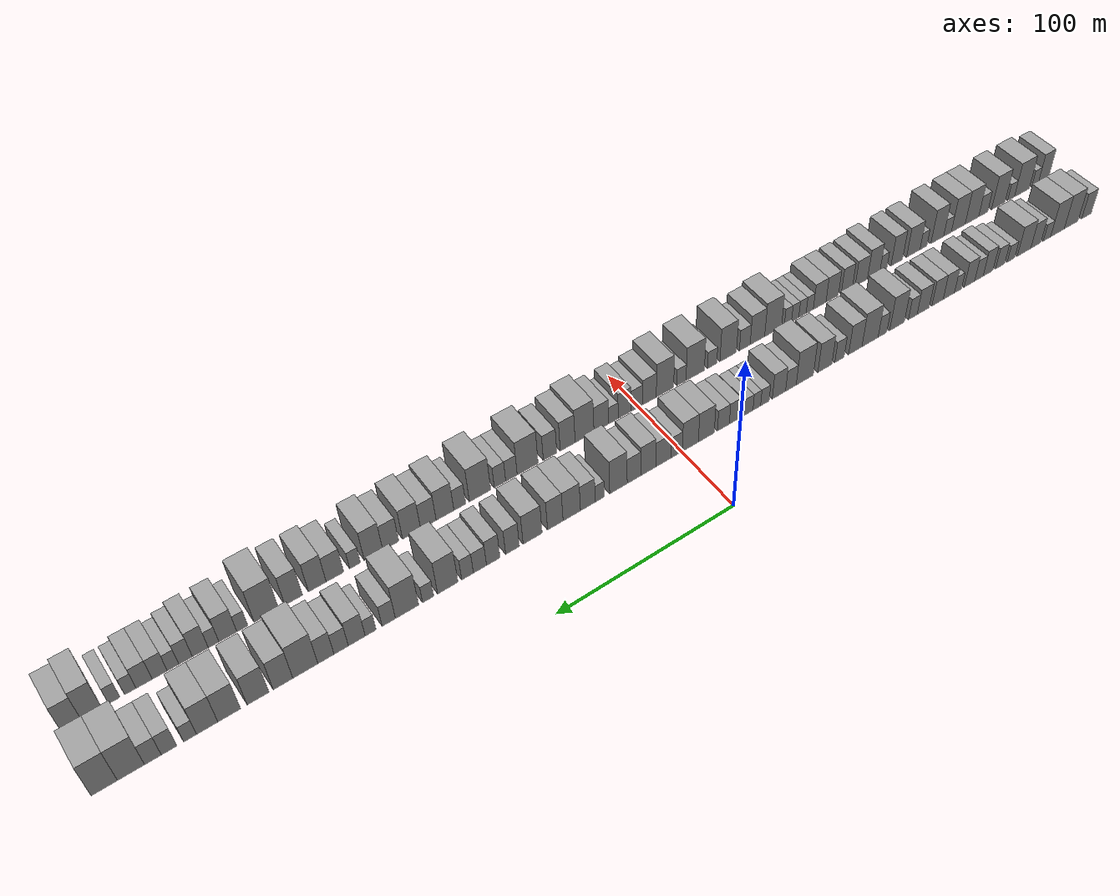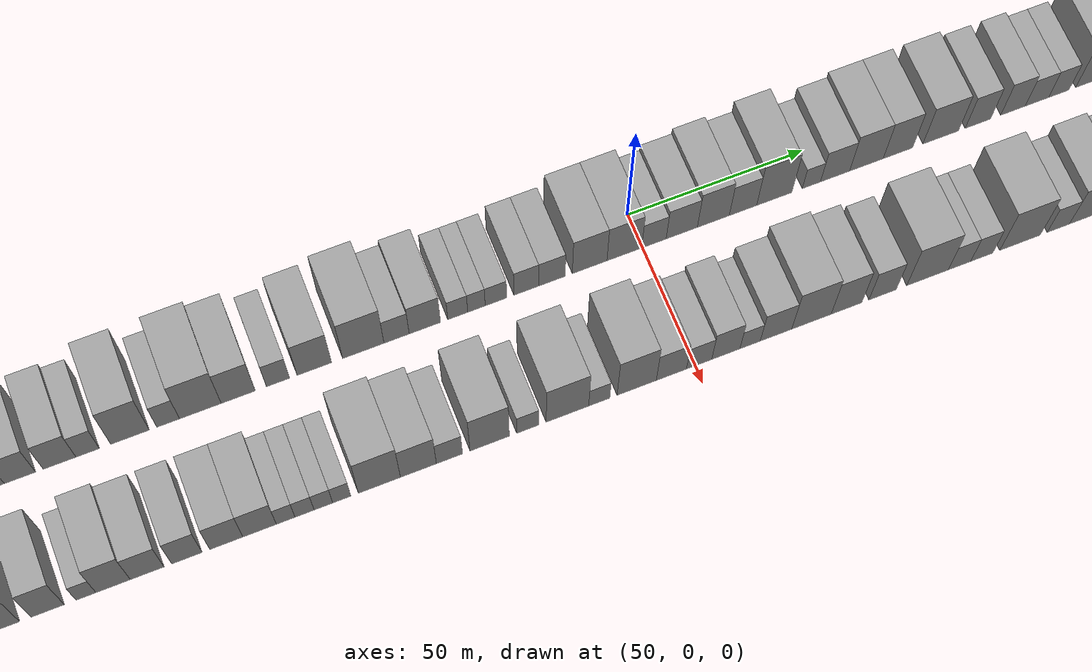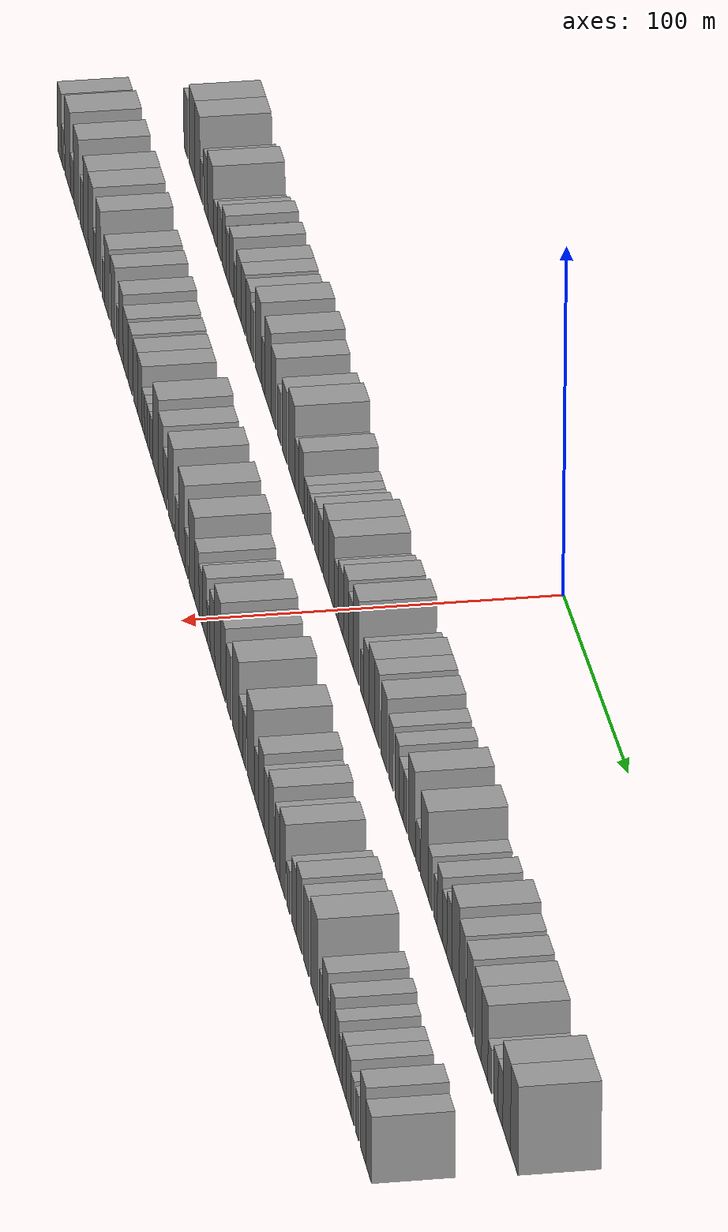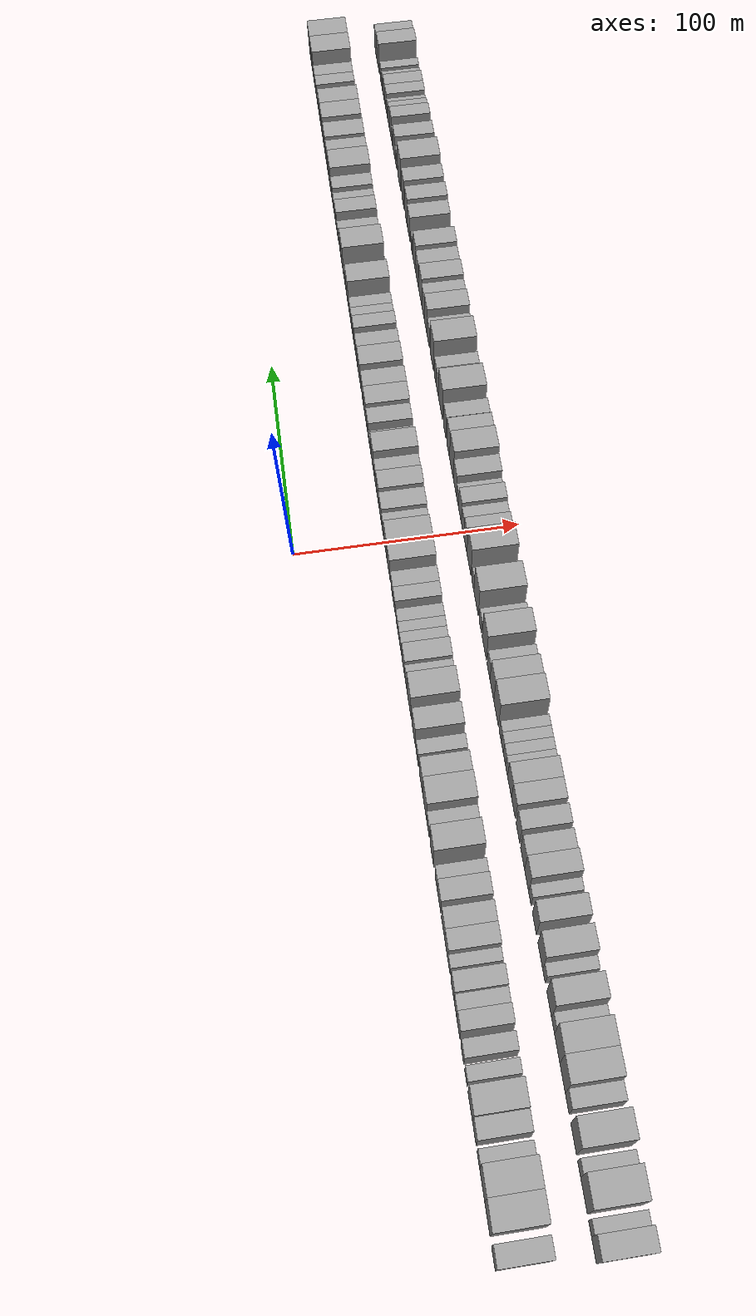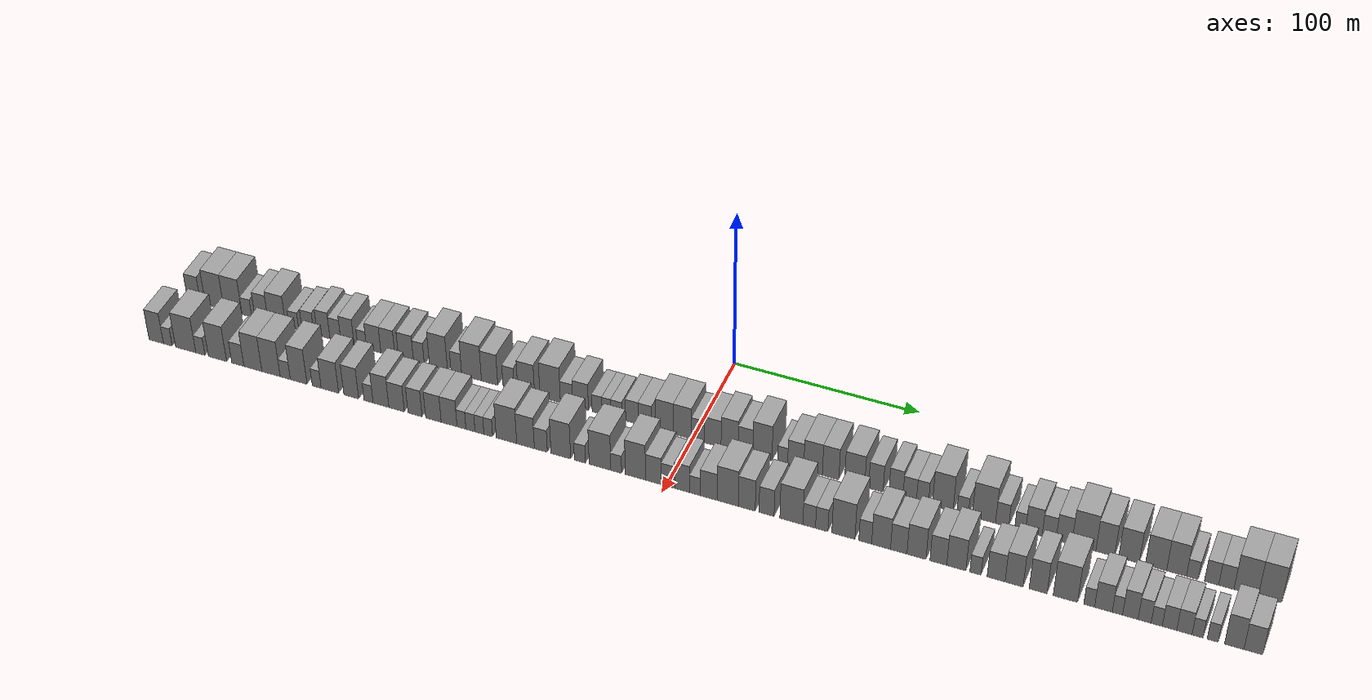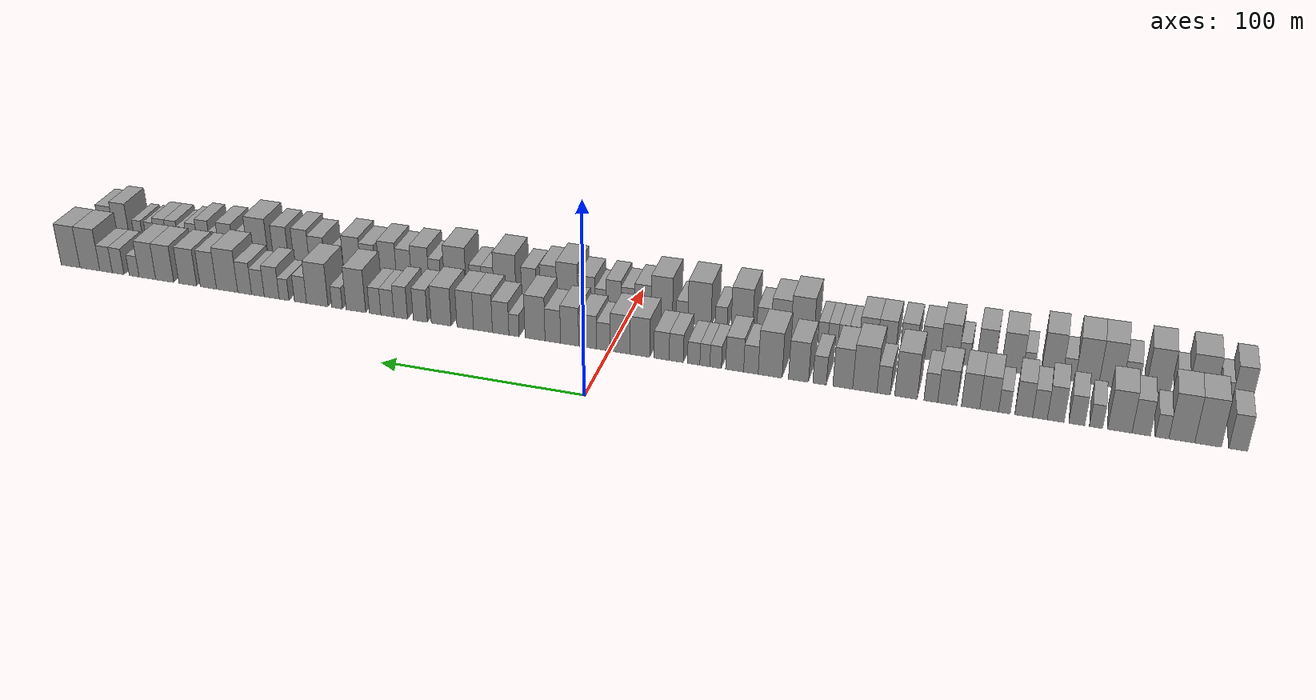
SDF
<sdf version="1.6">
 <world name="default">
  <scene>
   <sky><clouds><speed>12</speed></clouds></sky>
   <ambient>0.4 0.4 0.4 1</ambient>
   <background>0.7 0.7 0.7 1</background>
   <shadows>1</shadows>
  </scene>
  <gravity>0 0 -9.8066</gravity>
  <magnetic_field>6e-06 2.3e-05 -4.2e-05</magnetic_field>
  <physics default="0" name="default_physics" type="ode">
   <ode>
    <solver>
     <type>quick</type>
     <iters>10</iters>
     <sor>1.0</sor>
     <use_dynamic_moi_rescaling>0</use_dynamic_moi_rescaling>
    </solver>
    <constraints>
     <cfm>0</cfm>
     <erp>0.2</erp>
     <contact_max_correcting_vel>100</contact_max_correcting_vel>
     <contact_surface_layer>0.001</contact_surface_layer>
    </constraints>
   </ode>
   <max_step_size>0.004</max_step_size>
   <real_time_factor>1</real_time_factor>
   <real_time_update_rate>250</real_time_update_rate>
  </physics>
  <light name="sun" type="directional">
   <pose>0 0 10 0 0 0</pose>
   <diffuse>0.8 0.8 0.8 1</diffuse>
   <specular>0.2 0.2 0.2 1</specular>
   <attenuation>
    <range>1000</range>
    <constant>0.9</constant>
    <linear>0.01</linear>
    <quadratic>0.001</quadratic>
   </attenuation>
   <direction>-0.5 0.1 -0.9</direction>
  </light>
  <model name="building_1">
   <static>1</static>
   <pose>50.0000 -283.1225 0 0.000000 0.000000 0.000000</pose>
   <link name="link">
    <pose>0 0 9.00 0 0 0</pose>
    <collision name="collision"><geometry><box><size>20.0000 7.7550 18.0000</size></box></geometry></collision>
    <visual name="visual">
     <cast_shadows>0</cast_shadows>
     <geometry><box><size>20.0000 7.7550 18.0000</size></box></geometry>
     <material>
      <script>
       <uri>model://grey_wall/materials/scripts</uri>
       <uri>model://grey_wall/materials/textures</uri>
       <name>vrc/grey_wall</name>
      </script>
     </material>
    </visual>
   </link>
  </model>
  <model name="building_2">
   <static>1</static>
   <pose>50.0000 -270.7268 0 0.000000 0.000000 0.000000</pose>
   <link name="link">
    <pose>0 0 12.00 0 0 0</pose>
    <collision name="collision"><geometry><box><size>20.0000 11.0365 24.0000</size></box></geometry></collision>
    <visual name="visual">
     <cast_shadows>0</cast_shadows>
     <geometry><box><size>20.0000 11.0365 24.0000</size></box></geometry>
     <material>
      <script>
       <uri>model://grey_wall/materials/scripts</uri>
       <uri>model://grey_wall/materials/textures</uri>
       <name>vrc/grey_wall</name>
      </script>
     </material>
    </visual>
   </link>
  </model>
  <model name="building_3">
   <static>1</static>
   <pose>50.0000 -259.8181 0 0.000000 0.000000 0.000000</pose>
   <link name="link">
    <pose>0 0 12.00 0 0 0</pose>
    <collision name="collision"><geometry><box><size>20.0000 10.7809 24.0000</size></box></geometry></collision>
    <visual name="visual">
     <cast_shadows>0</cast_shadows>
     <geometry><box><size>20.0000 10.7809 24.0000</size></box></geometry>
     <material>
      <script>
       <uri>model://grey_wall/materials/scripts</uri>
       <uri>model://grey_wall/materials/textures</uri>
       <name>vrc/grey_wall</name>
      </script>
     </material>
    </visual>
   </link>
  </model>
  <model name="building_4">
   <static>1</static>
   <pose>50.0000 -251.5832 0 0.000000 0.000000 0.000000</pose>
   <link name="link">
    <pose>0 0 6.00 0 0 0</pose>
    <collision name="collision"><geometry><box><size>20.0000 5.6888 12.0000</size></box></geometry></collision>
    <visual name="visual">
     <cast_shadows>0</cast_shadows>
     <geometry><box><size>20.0000 5.6888 12.0000</size></box></geometry>
     <material>
      <script>
       <uri>model://grey_wall/materials/scripts</uri>
       <uri>model://grey_wall/materials/textures</uri>
       <name>vrc/grey_wall</name>
      </script>
     </material>
    </visual>
   </link>
  </model>
  <model name="building_5">
   <static>1</static>
   <pose>50.0000 -242.8581 0 0.000000 0.000000 0.000000</pose>
   <link name="link">
    <pose>0 0 9.00 0 0 0</pose>
    <collision name="collision"><geometry><box><size>20.0000 7.7615 18.0000</size></box></geometry></collision>
    <visual name="visual">
     <cast_shadows>0</cast_shadows>
     <geometry><box><size>20.0000 7.7615 18.0000</size></box></geometry>
     <material>
      <script>
       <uri>model://grey_wall/materials/scripts</uri>
       <uri>model://grey_wall/materials/textures</uri>
       <name>vrc/grey_wall</name>
      </script>
     </material>
    </visual>
   </link>
  </model>
  <model name="building_6">
   <static>1</static>
   <pose>50.0000 -233.7783 0 0.000000 0.000000 0.000000</pose>
   <link name="link">
    <pose>0 0 10.50 0 0 0</pose>
    <collision name="collision"><geometry><box><size>20.0000 10.3982 21.0000</size></box></geometry></collision>
    <visual name="visual">
     <cast_shadows>0</cast_shadows>
     <geometry><box><size>20.0000 10.3982 21.0000</size></box></geometry>
     <material>
      <script>
       <uri>model://grey_wall/materials/scripts</uri>
       <uri>model://grey_wall/materials/textures</uri>
       <name>vrc/grey_wall</name>
      </script>
     </material>
    </visual>
   </link>
  </model>
  <model name="building_7">
   <static>1</static>
   <pose>50.0000 -223.7424 0 0.000000 0.000000 0.000000</pose>
   <link name="link">
    <pose>0 0 6.00 0 0 0</pose>
    <collision name="collision"><geometry><box><size>20.0000 5.6735 12.0000</size></box></geometry></collision>
    <visual name="visual">
     <cast_shadows>0</cast_shadows>
     <geometry><box><size>20.0000 5.6735 12.0000</size></box></geometry>
     <material>
      <script>
       <uri>model://grey_wall/materials/scripts</uri>
       <uri>model://grey_wall/materials/textures</uri>
       <name>vrc/grey_wall</name>
      </script>
     </material>
    </visual>
   </link>
  </model>
  <model name="building_8">
   <static>1</static>
   <pose>50.0000 -215.4762 0 0.000000 0.000000 0.000000</pose>
   <link name="link">
    <pose>0 0 7.50 0 0 0</pose>
    <collision name="collision"><geometry><box><size>20.0000 6.8589 15.0000</size></box></geometry></collision>
    <visual name="visual">
     <cast_shadows>0</cast_shadows>
     <geometry><box><size>20.0000 6.8589 15.0000</size></box></geometry>
     <material>
      <script>
       <uri>model://grey_wall/materials/scripts</uri>
       <uri>model://grey_wall/materials/textures</uri>
       <name>vrc/grey_wall</name>
      </script>
     </material>
    </visual>
   </link>
  </model>
  <model name="building_9">
   <static>1</static>
   <pose>50.0000 -206.3850 0 0.000000 0.000000 0.000000</pose>
   <link name="link">
    <pose>0 0 9.00 0 0 0</pose>
    <collision name="collision"><geometry><box><size>20.0000 7.3234 18.0000</size></box></geometry></collision>
    <visual name="visual">
     <cast_shadows>0</cast_shadows>
     <geometry><box><size>20.0000 7.3234 18.0000</size></box></geometry>
     <material>
      <script>
       <uri>model://grey_wall/materials/scripts</uri>
       <uri>model://grey_wall/materials/textures</uri>
       <name>vrc/grey_wall</name>
      </script>
     </material>
    </visual>
   </link>
  </model>
  <model name="building_10">
   <static>1</static>
   <pose>50.0000 -199.5266 0 0.000000 0.000000 0.000000</pose>
   <link name="link">
    <pose>0 0 7.50 0 0 0</pose>
    <collision name="collision"><geometry><box><size>20.0000 6.3935 15.0000</size></box></geometry></collision>
    <visual name="visual">
     <cast_shadows>0</cast_shadows>
     <geometry><box><size>20.0000 6.3935 15.0000</size></box></geometry>
     <material>
      <script>
       <uri>model://grey_wall/materials/scripts</uri>
       <uri>model://grey_wall/materials/textures</uri>
       <name>vrc/grey_wall</name>
      </script>
     </material>
    </visual>
   </link>
  </model>
  <model name="building_11">
   <static>1</static>
   <pose>50.0000 -192.4735 0 0.000000 0.000000 0.000000</pose>
   <link name="link">
    <pose>0 0 9.00 0 0 0</pose>
    <collision name="collision"><geometry><box><size>20.0000 7.7126 18.0000</size></box></geometry></collision>
    <visual name="visual">
     <cast_shadows>0</cast_shadows>
     <geometry><box><size>20.0000 7.7126 18.0000</size></box></geometry>
     <material>
      <script>
       <uri>model://grey_wall/materials/scripts</uri>
       <uri>model://grey_wall/materials/textures</uri>
       <name>vrc/grey_wall</name>
      </script>
     </material>
    </visual>
   </link>
  </model>
  <model name="building_12">
   <static>1</static>
   <pose>50.0000 -184.0339 0 0.000000 0.000000 0.000000</pose>
   <link name="link">
    <pose>0 0 6.00 0 0 0</pose>
    <collision name="collision"><geometry><box><size>20.0000 5.1668 12.0000</size></box></geometry></collision>
    <visual name="visual">
     <cast_shadows>0</cast_shadows>
     <geometry><box><size>20.0000 5.1668 12.0000</size></box></geometry>
     <material>
      <script>
       <uri>model://grey_wall/materials/scripts</uri>
       <uri>model://grey_wall/materials/textures</uri>
       <name>vrc/grey_wall</name>
      </script>
     </material>
    </visual>
   </link>
  </model>
  <model name="building_13">
   <static>1</static>
   <pose>50.0000 -177.3395 0 0.000000 0.000000 0.000000</pose>
   <link name="link">
    <pose>0 0 9.00 0 0 0</pose>
    <collision name="collision"><geometry><box><size>20.0000 8.2220 18.0000</size></box></geometry></collision>
    <visual name="visual">
     <cast_shadows>0</cast_shadows>
     <geometry><box><size>20.0000 8.2220 18.0000</size></box></geometry>
     <material>
      <script>
       <uri>model://grey_wall/materials/scripts</uri>
       <uri>model://grey_wall/materials/textures</uri>
       <name>vrc/grey_wall</name>
      </script>
     </material>
    </visual>
   </link>
  </model>
  <model name="building_14">
   <static>1</static>
   <pose>50.0000 -169.1463 0 0.000000 0.000000 0.000000</pose>
   <link name="link">
    <pose>0 0 9.00 0 0 0</pose>
    <collision name="collision"><geometry><box><size>20.0000 8.1645 18.0000</size></box></geometry></collision>
    <visual name="visual">
     <cast_shadows>0</cast_shadows>
     <geometry><box><size>20.0000 8.1645 18.0000</size></box></geometry>
     <material>
      <script>
       <uri>model://grey_wall/materials/scripts</uri>
       <uri>model://grey_wall/materials/textures</uri>
       <name>vrc/grey_wall</name>
      </script>
     </material>
    </visual>
   </link>
  </model>
  <model name="building_15">
   <static>1</static>
   <pose>50.0000 -158.7706 0 0.000000 0.000000 0.000000</pose>
   <link name="link">
    <pose>0 0 9.00 0 0 0</pose>
    <collision name="collision"><geometry><box><size>20.0000 8.5869 18.0000</size></box></geometry></collision>
    <visual name="visual">
     <cast_shadows>0</cast_shadows>
     <geometry><box><size>20.0000 8.5869 18.0000</size></box></geometry>
     <material>
      <script>
       <uri>model://grey_wall/materials/scripts</uri>
       <uri>model://grey_wall/materials/textures</uri>
       <name>vrc/grey_wall</name>
      </script>
     </material>
    </visual>
   </link>
  </model>
  <model name="building_16">
   <static>1</static>
   <pose>50.0000 -151.3988 0 0.000000 0.000000 0.000000</pose>
   <link name="link">
    <pose>0 0 7.50 0 0 0</pose>
    <collision name="collision"><geometry><box><size>20.0000 6.1567 15.0000</size></box></geometry></collision>
    <visual name="visual">
     <cast_shadows>0</cast_shadows>
     <geometry><box><size>20.0000 6.1567 15.0000</size></box></geometry>
     <material>
      <script>
       <uri>model://grey_wall/materials/scripts</uri>
       <uri>model://grey_wall/materials/textures</uri>
       <name>vrc/grey_wall</name>
      </script>
     </material>
    </visual>
   </link>
  </model>
  <model name="building_17">
   <static>1</static>
   <pose>50.0000 -140.2153 0 0.000000 0.000000 0.000000</pose>
   <link name="link">
    <pose>0 0 12.00 0 0 0</pose>
    <collision name="collision"><geometry><box><size>20.0000 10.2103 24.0000</size></box></geometry></collision>
    <visual name="visual">
     <cast_shadows>0</cast_shadows>
     <geometry><box><size>20.0000 10.2103 24.0000</size></box></geometry>
     <material>
      <script>
       <uri>model://grey_wall/materials/scripts</uri>
       <uri>model://grey_wall/materials/textures</uri>
       <name>vrc/grey_wall</name>
      </script>
     </material>
    </visual>
   </link>
  </model>
  <model name="building_18">
   <static>1</static>
   <pose>50.0000 -130.0983 0 0.000000 0.000000 0.000000</pose>
   <link name="link">
    <pose>0 0 7.50 0 0 0</pose>
    <collision name="collision"><geometry><box><size>20.0000 6.0237 15.0000</size></box></geometry></collision>
    <visual name="visual">
     <cast_shadows>0</cast_shadows>
     <geometry><box><size>20.0000 6.0237 15.0000</size></box></geometry>
     <material>
      <script>
       <uri>model://grey_wall/materials/scripts</uri>
       <uri>model://grey_wall/materials/textures</uri>
       <name>vrc/grey_wall</name>
      </script>
     </material>
    </visual>
   </link>
  </model>
  <model name="building_19">
   <static>1</static>
   <pose>50.0000 -121.5091 0 0.000000 0.000000 0.000000</pose>
   <link name="link">
    <pose>0 0 12.00 0 0 0</pose>
    <collision name="collision"><geometry><box><size>20.0000 11.1546 24.0000</size></box></geometry></collision>
    <visual name="visual">
     <cast_shadows>0</cast_shadows>
     <geometry><box><size>20.0000 11.1546 24.0000</size></box></geometry>
     <material>
      <script>
       <uri>model://grey_wall/materials/scripts</uri>
       <uri>model://grey_wall/materials/textures</uri>
       <name>vrc/grey_wall</name>
      </script>
     </material>
    </visual>
   </link>
  </model>
  <model name="building_20">
   <static>1</static>
   <pose>50.0000 -111.3665 0 0.000000 0.000000 0.000000</pose>
   <link name="link">
    <pose>0 0 10.50 0 0 0</pose>
    <collision name="collision"><geometry><box><size>20.0000 9.1307 21.0000</size></box></geometry></collision>
    <visual name="visual">
     <cast_shadows>0</cast_shadows>
     <geometry><box><size>20.0000 9.1307 21.0000</size></box></geometry>
     <material>
      <script>
       <uri>model://grey_wall/materials/scripts</uri>
       <uri>model://grey_wall/materials/textures</uri>
       <name>vrc/grey_wall</name>
      </script>
     </material>
    </visual>
   </link>
  </model>
  <model name="building_21">
   <static>1</static>
   <pose>50.0000 -100.6610 0 0.000000 0.000000 0.000000</pose>
   <link name="link">
    <pose>0 0 7.50 0 0 0</pose>
    <collision name="collision"><geometry><box><size>20.0000 6.2802 15.0000</size></box></geometry></collision>
    <visual name="visual">
     <cast_shadows>0</cast_shadows>
     <geometry><box><size>20.0000 6.2802 15.0000</size></box></geometry>
     <material>
      <script>
       <uri>model://grey_wall/materials/scripts</uri>
       <uri>model://grey_wall/materials/textures</uri>
       <name>vrc/grey_wall</name>
      </script>
     </material>
    </visual>
   </link>
  </model>
  <model name="building_22">
   <static>1</static>
   <pose>50.0000 -90.8468 0 0.000000 0.000000 0.000000</pose>
   <link name="link">
    <pose>0 0 10.50 0 0 0</pose>
    <collision name="collision"><geometry><box><size>20.0000 9.3482 21.0000</size></box></geometry></collision>
    <visual name="visual">
     <cast_shadows>0</cast_shadows>
     <geometry><box><size>20.0000 9.3482 21.0000</size></box></geometry>
     <material>
      <script>
       <uri>model://grey_wall/materials/scripts</uri>
       <uri>model://grey_wall/materials/textures</uri>
       <name>vrc/grey_wall</name>
      </script>
     </material>
    </visual>
   </link>
  </model>
  <model name="building_23">
   <static>1</static>
   <pose>50.0000 -77.5330 0 0.000000 0.000000 0.000000</pose>
   <link name="link">
    <pose>0 0 12.00 0 0 0</pose>
    <collision name="collision"><geometry><box><size>20.0000 11.2795 24.0000</size></box></geometry></collision>
    <visual name="visual">
     <cast_shadows>0</cast_shadows>
     <geometry><box><size>20.0000 11.2795 24.0000</size></box></geometry>
     <material>
      <script>
       <uri>model://grey_wall/materials/scripts</uri>
       <uri>model://grey_wall/materials/textures</uri>
       <name>vrc/grey_wall</name>
      </script>
     </material>
    </visual>
   </link>
  </model>
  <model name="building_24">
   <static>1</static>
   <pose>50.0000 -68.4396 0 0.000000 0.000000 0.000000</pose>
   <link name="link">
    <pose>0 0 7.50 0 0 0</pose>
    <collision name="collision"><geometry><box><size>20.0000 6.9074 15.0000</size></box></geometry></collision>
    <visual name="visual">
     <cast_shadows>0</cast_shadows>
     <geometry><box><size>20.0000 6.9074 15.0000</size></box></geometry>
     <material>
      <script>
       <uri>model://grey_wall/materials/scripts</uri>
       <uri>model://grey_wall/materials/textures</uri>
       <name>vrc/grey_wall</name>
      </script>
     </material>
    </visual>
   </link>
  </model>
  <model name="building_25">
   <static>1</static>
   <pose>50.0000 -60.6884 0 0.000000 0.000000 0.000000</pose>
   <link name="link">
    <pose>0 0 9.00 0 0 0</pose>
    <collision name="collision"><geometry><box><size>20.0000 8.5951 18.0000</size></box></geometry></collision>
    <visual name="visual">
     <cast_shadows>0</cast_shadows>
     <geometry><box><size>20.0000 8.5951 18.0000</size></box></geometry>
     <material>
      <script>
       <uri>model://grey_wall/materials/scripts</uri>
       <uri>model://grey_wall/materials/textures</uri>
       <name>vrc/grey_wall</name>
      </script>
     </material>
    </visual>
   </link>
  </model>
  <model name="building_26">
   <static>1</static>
   <pose>50.0000 -51.6435 0 0.000000 0.000000 0.000000</pose>
   <link name="link">
    <pose>0 0 6.00 0 0 0</pose>
    <collision name="collision"><geometry><box><size>20.0000 5.4947 12.0000</size></box></geometry></collision>
    <visual name="visual">
     <cast_shadows>0</cast_shadows>
     <geometry><box><size>20.0000 5.4947 12.0000</size></box></geometry>
     <material>
      <script>
       <uri>model://grey_wall/materials/scripts</uri>
       <uri>model://grey_wall/materials/textures</uri>
       <name>vrc/grey_wall</name>
      </script>
     </material>
    </visual>
   </link>
  </model>
  <model name="building_27">
   <static>1</static>
   <pose>50.0000 -46.4779 0 0.000000 0.000000 0.000000</pose>
   <link name="link">
    <pose>0 0 6.00 0 0 0</pose>
    <collision name="collision"><geometry><box><size>20.0000 4.8365 12.0000</size></box></geometry></collision>
    <visual name="visual">
     <cast_shadows>0</cast_shadows>
     <geometry><box><size>20.0000 4.8365 12.0000</size></box></geometry>
     <material>
      <script>
       <uri>model://grey_wall/materials/scripts</uri>
       <uri>model://grey_wall/materials/textures</uri>
       <name>vrc/grey_wall</name>
      </script>
     </material>
    </visual>
   </link>
  </model>
  <model name="building_28">
   <static>1</static>
   <pose>50.0000 -41.0760 0 0.000000 0.000000 0.000000</pose>
   <link name="link">
    <pose>0 0 6.00 0 0 0</pose>
    <collision name="collision"><geometry><box><size>20.0000 5.9673 12.0000</size></box></geometry></collision>
    <visual name="visual">
     <cast_shadows>0</cast_shadows>
     <geometry><box><size>20.0000 5.9673 12.0000</size></box></geometry>
     <material>
      <script>
       <uri>model://grey_wall/materials/scripts</uri>
       <uri>model://grey_wall/materials/textures</uri>
       <name>vrc/grey_wall</name>
      </script>
     </material>
    </visual>
   </link>
  </model>
  <model name="building_29">
   <static>1</static>
   <pose>50.0000 -32.6428 0 0.000000 0.000000 0.000000</pose>
   <link name="link">
    <pose>0 0 7.50 0 0 0</pose>
    <collision name="collision"><geometry><box><size>20.0000 6.8992 15.0000</size></box></geometry></collision>
    <visual name="visual">
     <cast_shadows>0</cast_shadows>
     <geometry><box><size>20.0000 6.8992 15.0000</size></box></geometry>
     <material>
      <script>
       <uri>model://grey_wall/materials/scripts</uri>
       <uri>model://grey_wall/materials/textures</uri>
       <name>vrc/grey_wall</name>
      </script>
     </material>
    </visual>
   </link>
  </model>
  <model name="building_30">
   <static>1</static>
   <pose>50.0000 -25.5044 0 0.000000 0.000000 0.000000</pose>
   <link name="link">
    <pose>0 0 7.50 0 0 0</pose>
    <collision name="collision"><geometry><box><size>20.0000 7.3777 15.0000</size></box></geometry></collision>
    <visual name="visual">
     <cast_shadows>0</cast_shadows>
     <geometry><box><size>20.0000 7.3777 15.0000</size></box></geometry>
     <material>
      <script>
       <uri>model://grey_wall/materials/scripts</uri>
       <uri>model://grey_wall/materials/textures</uri>
       <name>vrc/grey_wall</name>
      </script>
     </material>
    </visual>
   </link>
  </model>
  <model name="building_31">
   <static>1</static>
   <pose>50.0000 -14.9525 0 0.000000 0.000000 0.000000</pose>
   <link name="link">
    <pose>0 0 10.50 0 0 0</pose>
    <collision name="collision"><geometry><box><size>20.0000 9.7260 21.0000</size></box></geometry></collision>
    <visual name="visual">
     <cast_shadows>0</cast_shadows>
     <geometry><box><size>20.0000 9.7260 21.0000</size></box></geometry>
     <material>
      <script>
       <uri>model://grey_wall/materials/scripts</uri>
       <uri>model://grey_wall/materials/textures</uri>
       <name>vrc/grey_wall</name>
      </script>
     </material>
    </visual>
   </link>
  </model>
  <model name="building_32">
   <static>1</static>
   <pose>50.0000 -5.2037 0 0.000000 0.000000 0.000000</pose>
   <link name="link">
    <pose>0 0 10.50 0 0 0</pose>
    <collision name="collision"><geometry><box><size>20.0000 9.7716 21.0000</size></box></geometry></collision>
    <visual name="visual">
     <cast_shadows>0</cast_shadows>
     <geometry><box><size>20.0000 9.7716 21.0000</size></box></geometry>
     <material>
      <script>
       <uri>model://grey_wall/materials/scripts</uri>
       <uri>model://grey_wall/materials/textures</uri>
       <name>vrc/grey_wall</name>
      </script>
     </material>
    </visual>
   </link>
  </model>
  <model name="building_33">
   <static>1</static>
   <pose>50.0000 3.1521 0 0.000000 0.000000 0.000000</pose>
   <link name="link">
    <pose>0 0 7.50 0 0 0</pose>
    <collision name="collision"><geometry><box><size>20.0000 6.9400 15.0000</size></box></geometry></collision>
    <visual name="visual">
     <cast_shadows>0</cast_shadows>
     <geometry><box><size>20.0000 6.9400 15.0000</size></box></geometry>
     <material>
      <script>
       <uri>model://grey_wall/materials/scripts</uri>
       <uri>model://grey_wall/materials/textures</uri>
       <name>vrc/grey_wall</name>
      </script>
     </material>
    </visual>
   </link>
  </model>
  <model name="building_34">
   <static>1</static>
   <pose>50.0000 11.0460 0 0.000000 0.000000 0.000000</pose>
   <link name="link">
    <pose>0 0 9.00 0 0 0</pose>
    <collision name="collision"><geometry><box><size>20.0000 8.8478 18.0000</size></box></geometry></collision>
    <visual name="visual">
     <cast_shadows>0</cast_shadows>
     <geometry><box><size>20.0000 8.8478 18.0000</size></box></geometry>
     <material>
      <script>
       <uri>model://grey_wall/materials/scripts</uri>
       <uri>model://grey_wall/materials/textures</uri>
       <name>vrc/grey_wall</name>
      </script>
     </material>
    </visual>
   </link>
  </model>
  <model name="building_35">
   <static>1</static>
   <pose>50.0000 20.0284 0 0.000000 0.000000 0.000000</pose>
   <link name="link">
    <pose>0 0 10.50 0 0 0</pose>
    <collision name="collision"><geometry><box><size>20.0000 9.1170 21.0000</size></box></geometry></collision>
    <visual name="visual">
     <cast_shadows>0</cast_shadows>
     <geometry><box><size>20.0000 9.1170 21.0000</size></box></geometry>
     <material>
      <script>
       <uri>model://grey_wall/materials/scripts</uri>
       <uri>model://grey_wall/materials/textures</uri>
       <name>vrc/grey_wall</name>
      </script>
     </material>
    </visual>
   </link>
  </model>
  <model name="building_36">
   <static>1</static>
   <pose>50.0000 28.4956 0 0.000000 0.000000 0.000000</pose>
   <link name="link">
    <pose>0 0 9.00 0 0 0</pose>
    <collision name="collision"><geometry><box><size>20.0000 7.8173 18.0000</size></box></geometry></collision>
    <visual name="visual">
     <cast_shadows>0</cast_shadows>
     <geometry><box><size>20.0000 7.8173 18.0000</size></box></geometry>
     <material>
      <script>
       <uri>model://grey_wall/materials/scripts</uri>
       <uri>model://grey_wall/materials/textures</uri>
       <name>vrc/grey_wall</name>
      </script>
     </material>
    </visual>
   </link>
  </model>
  <model name="building_37">
   <static>1</static>
   <pose>50.0000 37.4809 0 0.000000 0.000000 0.000000</pose>
   <link name="link">
    <pose>0 0 12.00 0 0 0</pose>
    <collision name="collision"><geometry><box><size>20.0000 10.1533 24.0000</size></box></geometry></collision>
    <visual name="visual">
     <cast_shadows>0</cast_shadows>
     <geometry><box><size>20.0000 10.1533 24.0000</size></box></geometry>
     <material>
      <script>
       <uri>model://grey_wall/materials/scripts</uri>
       <uri>model://grey_wall/materials/textures</uri>
       <name>vrc/grey_wall</name>
      </script>
     </material>
    </visual>
   </link>
  </model>
  <model name="building_38">
   <static>1</static>
   <pose>50.0000 48.1774 0 0.000000 0.000000 0.000000</pose>
   <link name="link">
    <pose>0 0 6.00 0 0 0</pose>
    <collision name="collision"><geometry><box><size>20.0000 5.2396 12.0000</size></box></geometry></collision>
    <visual name="visual">
     <cast_shadows>0</cast_shadows>
     <geometry><box><size>20.0000 5.2396 12.0000</size></box></geometry>
     <material>
      <script>
       <uri>model://grey_wall/materials/scripts</uri>
       <uri>model://grey_wall/materials/textures</uri>
       <name>vrc/grey_wall</name>
      </script>
     </material>
    </visual>
   </link>
  </model>
  <model name="building_39">
   <static>1</static>
   <pose>50.0000 55.0235 0 0.000000 0.000000 0.000000</pose>
   <link name="link">
    <pose>0 0 9.00 0 0 0</pose>
    <collision name="collision"><geometry><box><size>20.0000 8.4526 18.0000</size></box></geometry></collision>
    <visual name="visual">
     <cast_shadows>0</cast_shadows>
     <geometry><box><size>20.0000 8.4526 18.0000</size></box></geometry>
     <material>
      <script>
       <uri>model://grey_wall/materials/scripts</uri>
       <uri>model://grey_wall/materials/textures</uri>
       <name>vrc/grey_wall</name>
      </script>
     </material>
    </visual>
   </link>
  </model>
  <model name="building_40">
   <static>1</static>
   <pose>50.0000 64.1418 0 0.000000 0.000000 0.000000</pose>
   <link name="link">
    <pose>0 0 10.50 0 0 0</pose>
    <collision name="collision"><geometry><box><size>20.0000 9.7840 21.0000</size></box></geometry></collision>
    <visual name="visual">
     <cast_shadows>0</cast_shadows>
     <geometry><box><size>20.0000 9.7840 21.0000</size></box></geometry>
     <material>
      <script>
       <uri>model://grey_wall/materials/scripts</uri>
       <uri>model://grey_wall/materials/textures</uri>
       <name>vrc/grey_wall</name>
      </script>
     </material>
    </visual>
   </link>
  </model>
  <model name="building_41">
   <static>1</static>
   <pose>50.0000 73.3404 0 0.000000 0.000000 0.000000</pose>
   <link name="link">
    <pose>0 0 10.50 0 0 0</pose>
    <collision name="collision"><geometry><box><size>20.0000 8.6131 21.0000</size></box></geometry></collision>
    <visual name="visual">
     <cast_shadows>0</cast_shadows>
     <geometry><box><size>20.0000 8.6131 21.0000</size></box></geometry>
     <material>
      <script>
       <uri>model://grey_wall/materials/scripts</uri>
       <uri>model://grey_wall/materials/textures</uri>
       <name>vrc/grey_wall</name>
      </script>
     </material>
    </visual>
   </link>
  </model>
  <model name="building_42">
   <static>1</static>
   <pose>50.0000 85.8703 0 0.000000 0.000000 0.000000</pose>
   <link name="link">
    <pose>0 0 10.50 0 0 0</pose>
    <collision name="collision"><geometry><box><size>20.0000 10.4467 21.0000</size></box></geometry></collision>
    <visual name="visual">
     <cast_shadows>0</cast_shadows>
     <geometry><box><size>20.0000 10.4467 21.0000</size></box></geometry>
     <material>
      <script>
       <uri>model://grey_wall/materials/scripts</uri>
       <uri>model://grey_wall/materials/textures</uri>
       <name>vrc/grey_wall</name>
      </script>
     </material>
    </visual>
   </link>
  </model>
  <model name="building_43">
   <static>1</static>
   <pose>50.0000 96.8396 0 0.000000 0.000000 0.000000</pose>
   <link name="link">
    <pose>0 0 9.00 0 0 0</pose>
    <collision name="collision"><geometry><box><size>20.0000 7.4919 18.0000</size></box></geometry></collision>
    <visual name="visual">
     <cast_shadows>0</cast_shadows>
     <geometry><box><size>20.0000 7.4919 18.0000</size></box></geometry>
     <material>
      <script>
       <uri>model://grey_wall/materials/scripts</uri>
       <uri>model://grey_wall/materials/textures</uri>
       <name>vrc/grey_wall</name>
      </script>
     </material>
    </visual>
   </link>
  </model>
  <model name="building_44">
   <static>1</static>
   <pose>50.0000 107.2097 0 0.000000 0.000000 0.000000</pose>
   <link name="link">
    <pose>0 0 9.00 0 0 0</pose>
    <collision name="collision"><geometry><box><size>20.0000 7.2483 18.0000</size></box></geometry></collision>
    <visual name="visual">
     <cast_shadows>0</cast_shadows>
     <geometry><box><size>20.0000 7.2483 18.0000</size></box></geometry>
     <material>
      <script>
       <uri>model://grey_wall/materials/scripts</uri>
       <uri>model://grey_wall/materials/textures</uri>
       <name>vrc/grey_wall</name>
      </script>
     </material>
    </visual>
   </link>
  </model>
  <model name="building_45">
   <static>1</static>
   <pose>50.0000 114.3079 0 0.000000 0.000000 0.000000</pose>
   <link name="link">
    <pose>0 0 7.50 0 0 0</pose>
    <collision name="collision"><geometry><box><size>20.0000 6.9482 15.0000</size></box></geometry></collision>
    <visual name="visual">
     <cast_shadows>0</cast_shadows>
     <geometry><box><size>20.0000 6.9482 15.0000</size></box></geometry>
     <material>
      <script>
       <uri>model://grey_wall/materials/scripts</uri>
       <uri>model://grey_wall/materials/textures</uri>
       <name>vrc/grey_wall</name>
      </script>
     </material>
    </visual>
   </link>
  </model>
  <model name="building_46">
   <static>1</static>
   <pose>50.0000 120.8372 0 0.000000 0.000000 0.000000</pose>
   <link name="link">
    <pose>0 0 7.50 0 0 0</pose>
    <collision name="collision"><geometry><box><size>20.0000 6.1103 15.0000</size></box></geometry></collision>
    <visual name="visual">
     <cast_shadows>0</cast_shadows>
     <geometry><box><size>20.0000 6.1103 15.0000</size></box></geometry>
     <material>
      <script>
       <uri>model://grey_wall/materials/scripts</uri>
       <uri>model://grey_wall/materials/textures</uri>
       <name>vrc/grey_wall</name>
      </script>
     </material>
    </visual>
   </link>
  </model>
  <model name="building_47">
   <static>1</static>
   <pose>50.0000 131.1710 0 0.000000 0.000000 0.000000</pose>
   <link name="link">
    <pose>0 0 12.00 0 0 0</pose>
    <collision name="collision"><geometry><box><size>20.0000 10.5573 24.0000</size></box></geometry></collision>
    <visual name="visual">
     <cast_shadows>0</cast_shadows>
     <geometry><box><size>20.0000 10.5573 24.0000</size></box></geometry>
     <material>
      <script>
       <uri>model://grey_wall/materials/scripts</uri>
       <uri>model://grey_wall/materials/textures</uri>
       <name>vrc/grey_wall</name>
      </script>
     </material>
    </visual>
   </link>
  </model>
  <model name="building_48">
   <static>1</static>
   <pose>50.0000 141.3286 0 0.000000 0.000000 0.000000</pose>
   <link name="link">
    <pose>0 0 6.00 0 0 0</pose>
    <collision name="collision"><geometry><box><size>20.0000 5.7578 12.0000</size></box></geometry></collision>
    <visual name="visual">
     <cast_shadows>0</cast_shadows>
     <geometry><box><size>20.0000 5.7578 12.0000</size></box></geometry>
     <material>
      <script>
       <uri>model://grey_wall/materials/scripts</uri>
       <uri>model://grey_wall/materials/textures</uri>
       <name>vrc/grey_wall</name>
      </script>
     </material>
    </visual>
   </link>
  </model>
  <model name="building_49">
   <static>1</static>
   <pose>50.0000 152.1058 0 0.000000 0.000000 0.000000</pose>
   <link name="link">
    <pose>0 0 12.00 0 0 0</pose>
    <collision name="collision"><geometry><box><size>20.0000 11.7966 24.0000</size></box></geometry></collision>
    <visual name="visual">
     <cast_shadows>0</cast_shadows>
     <geometry><box><size>20.0000 11.7966 24.0000</size></box></geometry>
     <material>
      <script>
       <uri>model://grey_wall/materials/scripts</uri>
       <uri>model://grey_wall/materials/textures</uri>
       <name>vrc/grey_wall</name>
      </script>
     </material>
    </visual>
   </link>
  </model>
  <model name="building_50">
   <static>1</static>
   <pose>50.0000 161.3283 0 0.000000 0.000000 0.000000</pose>
   <link name="link">
    <pose>0 0 7.50 0 0 0</pose>
    <collision name="collision"><geometry><box><size>20.0000 6.6484 15.0000</size></box></geometry></collision>
    <visual name="visual">
     <cast_shadows>0</cast_shadows>
     <geometry><box><size>20.0000 6.6484 15.0000</size></box></geometry>
     <material>
      <script>
       <uri>model://grey_wall/materials/scripts</uri>
       <uri>model://grey_wall/materials/textures</uri>
       <name>vrc/grey_wall</name>
      </script>
     </material>
    </visual>
   </link>
  </model>
  <model name="building_51">
   <static>1</static>
   <pose>50.0000 170.3522 0 0.000000 0.000000 0.000000</pose>
   <link name="link">
    <pose>0 0 6.00 0 0 0</pose>
    <collision name="collision"><geometry><box><size>20.0000 5.3995 12.0000</size></box></geometry></collision>
    <visual name="visual">
     <cast_shadows>0</cast_shadows>
     <geometry><box><size>20.0000 5.3995 12.0000</size></box></geometry>
     <material>
      <script>
       <uri>model://grey_wall/materials/scripts</uri>
       <uri>model://grey_wall/materials/textures</uri>
       <name>vrc/grey_wall</name>
      </script>
     </material>
    </visual>
   </link>
  </model>
  <model name="building_52">
   <static>1</static>
   <pose>50.0000 177.2040 0 0.000000 0.000000 0.000000</pose>
   <link name="link">
    <pose>0 0 9.00 0 0 0</pose>
    <collision name="collision"><geometry><box><size>20.0000 8.3040 18.0000</size></box></geometry></collision>
    <visual name="visual">
     <cast_shadows>0</cast_shadows>
     <geometry><box><size>20.0000 8.3040 18.0000</size></box></geometry>
     <material>
      <script>
       <uri>model://grey_wall/materials/scripts</uri>
       <uri>model://grey_wall/materials/textures</uri>
       <name>vrc/grey_wall</name>
      </script>
     </material>
    </visual>
   </link>
  </model>
  <model name="building_53">
   <static>1</static>
   <pose>50.0000 184.8605 0 0.000000 0.000000 0.000000</pose>
   <link name="link">
    <pose>0 0 7.50 0 0 0</pose>
    <collision name="collision"><geometry><box><size>20.0000 7.0092 15.0000</size></box></geometry></collision>
    <visual name="visual">
     <cast_shadows>0</cast_shadows>
     <geometry><box><size>20.0000 7.0092 15.0000</size></box></geometry>
     <material>
      <script>
       <uri>model://grey_wall/materials/scripts</uri>
       <uri>model://grey_wall/materials/textures</uri>
       <name>vrc/grey_wall</name>
      </script>
     </material>
    </visual>
   </link>
  </model>
  <model name="building_54">
   <static>1</static>
   <pose>50.0000 192.2796 0 0.000000 0.000000 0.000000</pose>
   <link name="link">
    <pose>0 0 9.00 0 0 0</pose>
    <collision name="collision"><geometry><box><size>20.0000 7.8289 18.0000</size></box></geometry></collision>
    <visual name="visual">
     <cast_shadows>0</cast_shadows>
     <geometry><box><size>20.0000 7.8289 18.0000</size></box></geometry>
     <material>
      <script>
       <uri>model://grey_wall/materials/scripts</uri>
       <uri>model://grey_wall/materials/textures</uri>
       <name>vrc/grey_wall</name>
      </script>
     </material>
    </visual>
   </link>
  </model>
  <model name="building_55">
   <static>1</static>
   <pose>50.0000 202.1434 0 0.000000 0.000000 0.000000</pose>
   <link name="link">
    <pose>0 0 12.00 0 0 0</pose>
    <collision name="collision"><geometry><box><size>20.0000 11.8985 24.0000</size></box></geometry></collision>
    <visual name="visual">
     <cast_shadows>0</cast_shadows>
     <geometry><box><size>20.0000 11.8985 24.0000</size></box></geometry>
     <material>
      <script>
       <uri>model://grey_wall/materials/scripts</uri>
       <uri>model://grey_wall/materials/textures</uri>
       <name>vrc/grey_wall</name>
      </script>
     </material>
    </visual>
   </link>
  </model>
  <model name="building_56">
   <static>1</static>
   <pose>50.0000 212.7062 0 0.000000 0.000000 0.000000</pose>
   <link name="link">
    <pose>0 0 10.50 0 0 0</pose>
    <collision name="collision"><geometry><box><size>20.0000 9.2271 21.0000</size></box></geometry></collision>
    <visual name="visual">
     <cast_shadows>0</cast_shadows>
     <geometry><box><size>20.0000 9.2271 21.0000</size></box></geometry>
     <material>
      <script>
       <uri>model://grey_wall/materials/scripts</uri>
       <uri>model://grey_wall/materials/textures</uri>
       <name>vrc/grey_wall</name>
      </script>
     </material>
    </visual>
   </link>
  </model>
  <model name="building_57">
   <static>1</static>
   <pose>50.0000 224.3722 0 0.000000 0.000000 0.000000</pose>
   <link name="link">
    <pose>0 0 10.50 0 0 0</pose>
    <collision name="collision"><geometry><box><size>20.0000 10.1051 21.0000</size></box></geometry></collision>
    <visual name="visual">
     <cast_shadows>0</cast_shadows>
     <geometry><box><size>20.0000 10.1051 21.0000</size></box></geometry>
     <material>
      <script>
       <uri>model://grey_wall/materials/scripts</uri>
       <uri>model://grey_wall/materials/textures</uri>
       <name>vrc/grey_wall</name>
      </script>
     </material>
    </visual>
   </link>
  </model>
  <model name="building_58">
   <static>1</static>
   <pose>50.0000 237.6212 0 0.000000 0.000000 0.000000</pose>
   <link name="link">
    <pose>0 0 10.50 0 0 0</pose>
    <collision name="collision"><geometry><box><size>20.0000 10.3929 21.0000</size></box></geometry></collision>
    <visual name="visual">
     <cast_shadows>0</cast_shadows>
     <geometry><box><size>20.0000 10.3929 21.0000</size></box></geometry>
     <material>
      <script>
       <uri>model://grey_wall/materials/scripts</uri>
       <uri>model://grey_wall/materials/textures</uri>
       <name>vrc/grey_wall</name>
      </script>
     </material>
    </visual>
   </link>
  </model>
  <model name="building_59">
   <static>1</static>
   <pose>50.0000 247.6309 0 0.000000 0.000000 0.000000</pose>
   <link name="link">
    <pose>0 0 10.50 0 0 0</pose>
    <collision name="collision"><geometry><box><size>20.0000 9.6265 21.0000</size></box></geometry></collision>
    <visual name="visual">
     <cast_shadows>0</cast_shadows>
     <geometry><box><size>20.0000 9.6265 21.0000</size></box></geometry>
     <material>
      <script>
       <uri>model://grey_wall/materials/scripts</uri>
       <uri>model://grey_wall/materials/textures</uri>
       <name>vrc/grey_wall</name>
      </script>
     </material>
    </visual>
   </link>
  </model>
  <model name="building_60">
   <static>1</static>
   <pose>50.0000 255.3122 0 0.000000 0.000000 0.000000</pose>
   <link name="link">
    <pose>0 0 6.00 0 0 0</pose>
    <collision name="collision"><geometry><box><size>20.0000 5.7360 12.0000</size></box></geometry></collision>
    <visual name="visual">
     <cast_shadows>0</cast_shadows>
     <geometry><box><size>20.0000 5.7360 12.0000</size></box></geometry>
     <material>
      <script>
       <uri>model://grey_wall/materials/scripts</uri>
       <uri>model://grey_wall/materials/textures</uri>
       <name>vrc/grey_wall</name>
      </script>
     </material>
    </visual>
   </link>
  </model>
  <model name="building_61">
   <static>1</static>
   <pose>50.0000 264.6094 0 0.000000 0.000000 0.000000</pose>
   <link name="link">
    <pose>0 0 7.50 0 0 0</pose>
    <collision name="collision"><geometry><box><size>20.0000 6.8584 15.0000</size></box></geometry></collision>
    <visual name="visual">
     <cast_shadows>0</cast_shadows>
     <geometry><box><size>20.0000 6.8584 15.0000</size></box></geometry>
     <material>
      <script>
       <uri>model://grey_wall/materials/scripts</uri>
       <uri>model://grey_wall/materials/textures</uri>
       <name>vrc/grey_wall</name>
      </script>
     </material>
    </visual>
   </link>
  </model>
  <model name="building_62">
   <static>1</static>
   <pose>50.0000 271.6974 0 0.000000 0.000000 0.000000</pose>
   <link name="link">
    <pose>0 0 7.50 0 0 0</pose>
    <collision name="collision"><geometry><box><size>20.0000 7.3177 15.0000</size></box></geometry></collision>
    <visual name="visual">
     <cast_shadows>0</cast_shadows>
     <geometry><box><size>20.0000 7.3177 15.0000</size></box></geometry>
     <material>
      <script>
       <uri>model://grey_wall/materials/scripts</uri>
       <uri>model://grey_wall/materials/textures</uri>
       <name>vrc/grey_wall</name>
      </script>
     </material>
    </visual>
   </link>
  </model>
  <model name="building_63">
   <static>1</static>
   <pose>50.0000 281.1941 0 0.000000 0.000000 0.000000</pose>
   <link name="link">
    <pose>0 0 12.00 0 0 0</pose>
    <collision name="collision"><geometry><box><size>20.0000 11.6757 24.0000</size></box></geometry></collision>
    <visual name="visual">
     <cast_shadows>0</cast_shadows>
     <geometry><box><size>20.0000 11.6757 24.0000</size></box></geometry>
     <material>
      <script>
       <uri>model://grey_wall/materials/scripts</uri>
       <uri>model://grey_wall/materials/textures</uri>
       <name>vrc/grey_wall</name>
      </script>
     </material>
    </visual>
   </link>
  </model>
  <model name="building_64">
   <static>1</static>
   <pose>50.0000 292.6309 0 0.000000 0.000000 0.000000</pose>
   <link name="link">
    <pose>0 0 12.00 0 0 0</pose>
    <collision name="collision"><geometry><box><size>20.0000 11.1978 24.0000</size></box></geometry></collision>
    <visual name="visual">
     <cast_shadows>0</cast_shadows>
     <geometry><box><size>20.0000 11.1978 24.0000</size></box></geometry>
     <material>
      <script>
       <uri>model://grey_wall/materials/scripts</uri>
       <uri>model://grey_wall/materials/textures</uri>
       <name>vrc/grey_wall</name>
      </script>
     </material>
    </visual>
   </link>
  </model>
  <model name="building_65">
   <static>1</static>
   <pose>85.0000 -285.7629 0 0.000000 0.000000 0.000000</pose>
   <link name="link">
    <pose>0 0 10.50 0 0 0</pose>
    <collision name="collision"><geometry><box><size>20.0000 8.4741 21.0000</size></box></geometry></collision>
    <visual name="visual">
     <cast_shadows>0</cast_shadows>
     <geometry><box><size>20.0000 8.4741 21.0000</size></box></geometry>
     <material>
      <script>
       <uri>model://grey_wall/materials/scripts</uri>
       <uri>model://grey_wall/materials/textures</uri>
       <name>vrc/grey_wall</name>
      </script>
     </material>
    </visual>
   </link>
  </model>
  <model name="building_66">
   <static>1</static>
   <pose>85.0000 -278.9423 0 0.000000 0.000000 0.000000</pose>
   <link name="link">
    <pose>0 0 6.00 0 0 0</pose>
    <collision name="collision"><geometry><box><size>20.0000 5.1671 12.0000</size></box></geometry></collision>
    <visual name="visual">
     <cast_shadows>0</cast_shadows>
     <geometry><box><size>20.0000 5.1671 12.0000</size></box></geometry>
     <material>
      <script>
       <uri>model://grey_wall/materials/scripts</uri>
       <uri>model://grey_wall/materials/textures</uri>
       <name>vrc/grey_wall</name>
      </script>
     </material>
    </visual>
   </link>
  </model>
  <model name="building_67">
   <static>1</static>
   <pose>85.0000 -268.4089 0 0.000000 0.000000 0.000000</pose>
   <link name="link">
    <pose>0 0 12.00 0 0 0</pose>
    <collision name="collision"><geometry><box><size>20.0000 11.8997 24.0000</size></box></geometry></collision>
    <visual name="visual">
     <cast_shadows>0</cast_shadows>
     <geometry><box><size>20.0000 11.8997 24.0000</size></box></geometry>
     <material>
      <script>
       <uri>model://grey_wall/materials/scripts</uri>
       <uri>model://grey_wall/materials/textures</uri>
       <name>vrc/grey_wall</name>
      </script>
     </material>
    </visual>
   </link>
  </model>
  <model name="building_68">
   <static>1</static>
   <pose>85.0000 -259.7599 0 0.000000 0.000000 0.000000</pose>
   <link name="link">
    <pose>0 0 6.00 0 0 0</pose>
    <collision name="collision"><geometry><box><size>20.0000 5.3983 12.0000</size></box></geometry></collision>
    <visual name="visual">
     <cast_shadows>0</cast_shadows>
     <geometry><box><size>20.0000 5.3983 12.0000</size></box></geometry>
     <material>
      <script>
       <uri>model://grey_wall/materials/scripts</uri>
       <uri>model://grey_wall/materials/textures</uri>
       <name>vrc/grey_wall</name>
      </script>
     </material>
    </visual>
   </link>
  </model>
  <model name="building_69">
   <static>1</static>
   <pose>85.0000 -249.7298 0 0.000000 0.000000 0.000000</pose>
   <link name="link">
    <pose>0 0 12.00 0 0 0</pose>
    <collision name="collision"><geometry><box><size>20.0000 10.6620 24.0000</size></box></geometry></collision>
    <visual name="visual">
     <cast_shadows>0</cast_shadows>
     <geometry><box><size>20.0000 10.6620 24.0000</size></box></geometry>
     <material>
      <script>
       <uri>model://grey_wall/materials/scripts</uri>
       <uri>model://grey_wall/materials/textures</uri>
       <name>vrc/grey_wall</name>
      </script>
     </material>
    </visual>
   </link>
  </model>
  <model name="building_70">
   <static>1</static>
   <pose>85.0000 -237.8536 0 0.000000 0.000000 0.000000</pose>
   <link name="link">
    <pose>0 0 7.50 0 0 0</pose>
    <collision name="collision"><geometry><box><size>20.0000 7.0904 15.0000</size></box></geometry></collision>
    <visual name="visual">
     <cast_shadows>0</cast_shadows>
     <geometry><box><size>20.0000 7.0904 15.0000</size></box></geometry>
     <material>
      <script>
       <uri>model://grey_wall/materials/scripts</uri>
       <uri>model://grey_wall/materials/textures</uri>
       <name>vrc/grey_wall</name>
      </script>
     </material>
    </visual>
   </link>
  </model>
  <model name="building_71">
   <static>1</static>
   <pose>85.0000 -229.0931 0 0.000000 0.000000 0.000000</pose>
   <link name="link">
    <pose>0 0 12.00 0 0 0</pose>
    <collision name="collision"><geometry><box><size>20.0000 10.4305 24.0000</size></box></geometry></collision>
    <visual name="visual">
     <cast_shadows>0</cast_shadows>
     <geometry><box><size>20.0000 10.4305 24.0000</size></box></geometry>
     <material>
      <script>
       <uri>model://grey_wall/materials/scripts</uri>
       <uri>model://grey_wall/materials/textures</uri>
       <name>vrc/grey_wall</name>
      </script>
     </material>
    </visual>
   </link>
  </model>
  <model name="building_72">
   <static>1</static>
   <pose>85.0000 -218.6038 0 0.000000 0.000000 0.000000</pose>
   <link name="link">
    <pose>0 0 12.00 0 0 0</pose>
    <collision name="collision"><geometry><box><size>20.0000 10.5480 24.0000</size></box></geometry></collision>
    <visual name="visual">
     <cast_shadows>0</cast_shadows>
     <geometry><box><size>20.0000 10.5480 24.0000</size></box></geometry>
     <material>
      <script>
       <uri>model://grey_wall/materials/scripts</uri>
       <uri>model://grey_wall/materials/textures</uri>
       <name>vrc/grey_wall</name>
      </script>
     </material>
    </visual>
   </link>
  </model>
  <model name="building_73">
   <static>1</static>
   <pose>85.0000 -210.4165 0 0.000000 0.000000 0.000000</pose>
   <link name="link">
    <pose>0 0 6.00 0 0 0</pose>
    <collision name="collision"><geometry><box><size>20.0000 5.8268 12.0000</size></box></geometry></collision>
    <visual name="visual">
     <cast_shadows>0</cast_shadows>
     <geometry><box><size>20.0000 5.8268 12.0000</size></box></geometry>
     <material>
      <script>
       <uri>model://grey_wall/materials/scripts</uri>
       <uri>model://grey_wall/materials/textures</uri>
       <name>vrc/grey_wall</name>
      </script>
     </material>
    </visual>
   </link>
  </model>
  <model name="building_74">
   <static>1</static>
   <pose>85.0000 -202.6964 0 0.000000 0.000000 0.000000</pose>
   <link name="link">
    <pose>0 0 12.00 0 0 0</pose>
    <collision name="collision"><geometry><box><size>20.0000 9.6134 24.0000</size></box></geometry></collision>
    <visual name="visual">
     <cast_shadows>0</cast_shadows>
     <geometry><box><size>20.0000 9.6134 24.0000</size></box></geometry>
     <material>
      <script>
       <uri>model://grey_wall/materials/scripts</uri>
       <uri>model://grey_wall/materials/textures</uri>
       <name>vrc/grey_wall</name>
      </script>
     </material>
    </visual>
   </link>
  </model>
  <model name="building_75">
   <static>1</static>
   <pose>85.0000 -192.3279 0 0.000000 0.000000 0.000000</pose>
   <link name="link">
    <pose>0 0 6.00 0 0 0</pose>
    <collision name="collision"><geometry><box><size>20.0000 5.1236 12.0000</size></box></geometry></collision>
    <visual name="visual">
     <cast_shadows>0</cast_shadows>
     <geometry><box><size>20.0000 5.1236 12.0000</size></box></geometry>
     <material>
      <script>
       <uri>model://grey_wall/materials/scripts</uri>
       <uri>model://grey_wall/materials/textures</uri>
       <name>vrc/grey_wall</name>
      </script>
     </material>
    </visual>
   </link>
  </model>
  <model name="building_76">
   <static>1</static>
   <pose>85.0000 -184.7940 0 0.000000 0.000000 0.000000</pose>
   <link name="link">
    <pose>0 0 10.50 0 0 0</pose>
    <collision name="collision"><geometry><box><size>20.0000 9.9442 21.0000</size></box></geometry></collision>
    <visual name="visual">
     <cast_shadows>0</cast_shadows>
     <geometry><box><size>20.0000 9.9442 21.0000</size></box></geometry>
     <material>
      <script>
       <uri>model://grey_wall/materials/scripts</uri>
       <uri>model://grey_wall/materials/textures</uri>
       <name>vrc/grey_wall</name>
      </script>
     </material>
    </visual>
   </link>
  </model>
  <model name="building_77">
   <static>1</static>
   <pose>85.0000 -172.6151 0 0.000000 0.000000 0.000000</pose>
   <link name="link">
    <pose>0 0 10.50 0 0 0</pose>
    <collision name="collision"><geometry><box><size>20.0000 8.4137 21.0000</size></box></geometry></collision>
    <visual name="visual">
     <cast_shadows>0</cast_shadows>
     <geometry><box><size>20.0000 8.4137 21.0000</size></box></geometry>
     <material>
      <script>
       <uri>model://grey_wall/materials/scripts</uri>
       <uri>model://grey_wall/materials/textures</uri>
       <name>vrc/grey_wall</name>
      </script>
     </material>
    </visual>
   </link>
  </model>
  <model name="building_78">
   <static>1</static>
   <pose>85.0000 -162.8400 0 0.000000 0.000000 0.000000</pose>
   <link name="link">
    <pose>0 0 6.00 0 0 0</pose>
    <collision name="collision"><geometry><box><size>20.0000 5.1365 12.0000</size></box></geometry></collision>
    <visual name="visual">
     <cast_shadows>0</cast_shadows>
     <geometry><box><size>20.0000 5.1365 12.0000</size></box></geometry>
     <material>
      <script>
       <uri>model://grey_wall/materials/scripts</uri>
       <uri>model://grey_wall/materials/textures</uri>
       <name>vrc/grey_wall</name>
      </script>
     </material>
    </visual>
   </link>
  </model>
  <model name="building_79">
   <static>1</static>
   <pose>85.0000 -155.8376 0 0.000000 0.000000 0.000000</pose>
   <link name="link">
    <pose>0 0 10.50 0 0 0</pose>
    <collision name="collision"><geometry><box><size>20.0000 8.8683 21.0000</size></box></geometry></collision>
    <visual name="visual">
     <cast_shadows>0</cast_shadows>
     <geometry><box><size>20.0000 8.8683 21.0000</size></box></geometry>
     <material>
      <script>
       <uri>model://grey_wall/materials/scripts</uri>
       <uri>model://grey_wall/materials/textures</uri>
       <name>vrc/grey_wall</name>
      </script>
     </material>
    </visual>
   </link>
  </model>
  <model name="building_80">
   <static>1</static>
   <pose>85.0000 -147.0338 0 0.000000 0.000000 0.000000</pose>
   <link name="link">
    <pose>0 0 9.00 0 0 0</pose>
    <collision name="collision"><geometry><box><size>20.0000 8.7394 18.0000</size></box></geometry></collision>
    <visual name="visual">
     <cast_shadows>0</cast_shadows>
     <geometry><box><size>20.0000 8.7394 18.0000</size></box></geometry>
     <material>
      <script>
       <uri>model://grey_wall/materials/scripts</uri>
       <uri>model://grey_wall/materials/textures</uri>
       <name>vrc/grey_wall</name>
      </script>
     </material>
    </visual>
   </link>
  </model>
  <model name="building_81">
   <static>1</static>
   <pose>85.0000 -136.7139 0 0.000000 0.000000 0.000000</pose>
   <link name="link">
    <pose>0 0 9.00 0 0 0</pose>
    <collision name="collision"><geometry><box><size>20.0000 7.9003 18.0000</size></box></geometry></collision>
    <visual name="visual">
     <cast_shadows>0</cast_shadows>
     <geometry><box><size>20.0000 7.9003 18.0000</size></box></geometry>
     <material>
      <script>
       <uri>model://grey_wall/materials/scripts</uri>
       <uri>model://grey_wall/materials/textures</uri>
       <name>vrc/grey_wall</name>
      </script>
     </material>
    </visual>
   </link>
  </model>
  <model name="building_82">
   <static>1</static>
   <pose>85.0000 -126.4330 0 0.000000 0.000000 0.000000</pose>
   <link name="link">
    <pose>0 0 9.00 0 0 0</pose>
    <collision name="collision"><geometry><box><size>20.0000 8.6615 18.0000</size></box></geometry></collision>
    <visual name="visual">
     <cast_shadows>0</cast_shadows>
     <geometry><box><size>20.0000 8.6615 18.0000</size></box></geometry>
     <material>
      <script>
       <uri>model://grey_wall/materials/scripts</uri>
       <uri>model://grey_wall/materials/textures</uri>
       <name>vrc/grey_wall</name>
      </script>
     </material>
    </visual>
   </link>
  </model>
  <model name="building_83">
   <static>1</static>
   <pose>85.0000 -117.7067 0 0.000000 0.000000 0.000000</pose>
   <link name="link">
    <pose>0 0 9.00 0 0 0</pose>
    <collision name="collision"><geometry><box><size>20.0000 8.7912 18.0000</size></box></geometry></collision>
    <visual name="visual">
     <cast_shadows>0</cast_shadows>
     <geometry><box><size>20.0000 8.7912 18.0000</size></box></geometry>
     <material>
      <script>
       <uri>model://grey_wall/materials/scripts</uri>
       <uri>model://grey_wall/materials/textures</uri>
       <name>vrc/grey_wall</name>
      </script>
     </material>
    </visual>
   </link>
  </model>
  <model name="building_84">
   <static>1</static>
   <pose>85.0000 -110.8470 0 0.000000 0.000000 0.000000</pose>
   <link name="link">
    <pose>0 0 6.00 0 0 0</pose>
    <collision name="collision"><geometry><box><size>20.0000 4.9282 12.0000</size></box></geometry></collision>
    <visual name="visual">
     <cast_shadows>0</cast_shadows>
     <geometry><box><size>20.0000 4.9282 12.0000</size></box></geometry>
     <material>
      <script>
       <uri>model://grey_wall/materials/scripts</uri>
       <uri>model://grey_wall/materials/textures</uri>
       <name>vrc/grey_wall</name>
      </script>
     </material>
    </visual>
   </link>
  </model>
  <model name="building_85">
   <static>1</static>
   <pose>85.0000 -105.8679 0 0.000000 0.000000 0.000000</pose>
   <link name="link">
    <pose>0 0 6.00 0 0 0</pose>
    <collision name="collision"><geometry><box><size>20.0000 5.0300 12.0000</size></box></geometry></collision>
    <visual name="visual">
     <cast_shadows>0</cast_shadows>
     <geometry><box><size>20.0000 5.0300 12.0000</size></box></geometry>
     <material>
      <script>
       <uri>model://grey_wall/materials/scripts</uri>
       <uri>model://grey_wall/materials/textures</uri>
       <name>vrc/grey_wall</name>
      </script>
     </material>
    </visual>
   </link>
  </model>
  <model name="building_86">
   <static>1</static>
   <pose>85.0000 -100.8920 0 0.000000 0.000000 0.000000</pose>
   <link name="link">
    <pose>0 0 6.00 0 0 0</pose>
    <collision name="collision"><geometry><box><size>20.0000 4.9218 12.0000</size></box></geometry></collision>
    <visual name="visual">
     <cast_shadows>0</cast_shadows>
     <geometry><box><size>20.0000 4.9218 12.0000</size></box></geometry>
     <material>
      <script>
       <uri>model://grey_wall/materials/scripts</uri>
       <uri>model://grey_wall/materials/textures</uri>
       <name>vrc/grey_wall</name>
      </script>
     </material>
    </visual>
   </link>
  </model>
  <model name="building_87">
   <static>1</static>
   <pose>85.0000 -96.0195 0 0.000000 0.000000 0.000000</pose>
   <link name="link">
    <pose>0 0 6.00 0 0 0</pose>
    <collision name="collision"><geometry><box><size>20.0000 4.8233 12.0000</size></box></geometry></collision>
    <visual name="visual">
     <cast_shadows>0</cast_shadows>
     <geometry><box><size>20.0000 4.8233 12.0000</size></box></geometry>
     <material>
      <script>
       <uri>model://grey_wall/materials/scripts</uri>
       <uri>model://grey_wall/materials/textures</uri>
       <name>vrc/grey_wall</name>
      </script>
     </material>
    </visual>
   </link>
  </model>
  <model name="building_88">
   <static>1</static>
   <pose>85.0000 -85.9997 0 0.000000 0.000000 0.000000</pose>
   <link name="link">
    <pose>0 0 12.00 0 0 0</pose>
    <collision name="collision"><geometry><box><size>20.0000 11.2164 24.0000</size></box></geometry></collision>
    <visual name="visual">
     <cast_shadows>0</cast_shadows>
     <geometry><box><size>20.0000 11.2164 24.0000</size></box></geometry>
     <material>
      <script>
       <uri>model://grey_wall/materials/scripts</uri>
       <uri>model://grey_wall/materials/textures</uri>
       <name>vrc/grey_wall</name>
      </script>
     </material>
    </visual>
   </link>
  </model>
  <model name="building_89">
   <static>1</static>
   <pose>85.0000 -75.5719 0 0.000000 0.000000 0.000000</pose>
   <link name="link">
    <pose>0 0 10.50 0 0 0</pose>
    <collision name="collision"><geometry><box><size>20.0000 9.6392 21.0000</size></box></geometry></collision>
    <visual name="visual">
     <cast_shadows>0</cast_shadows>
     <geometry><box><size>20.0000 9.6392 21.0000</size></box></geometry>
     <material>
      <script>
       <uri>model://grey_wall/materials/scripts</uri>
       <uri>model://grey_wall/materials/textures</uri>
       <name>vrc/grey_wall</name>
      </script>
     </material>
    </visual>
   </link>
  </model>
  <model name="building_90">
   <static>1</static>
   <pose>85.0000 -67.2314 0 0.000000 0.000000 0.000000</pose>
   <link name="link">
    <pose>0 0 7.50 0 0 0</pose>
    <collision name="collision"><geometry><box><size>20.0000 7.0418 15.0000</size></box></geometry></collision>
    <visual name="visual">
     <cast_shadows>0</cast_shadows>
     <geometry><box><size>20.0000 7.0418 15.0000</size></box></geometry>
     <material>
      <script>
       <uri>model://grey_wall/materials/scripts</uri>
       <uri>model://grey_wall/materials/textures</uri>
       <name>vrc/grey_wall</name>
      </script>
     </material>
    </visual>
   </link>
  </model>
  <model name="building_91">
   <static>1</static>
   <pose>85.0000 -56.3849 0 0.000000 0.000000 0.000000</pose>
   <link name="link">
    <pose>0 0 12.00 0 0 0</pose>
    <collision name="collision"><geometry><box><size>20.0000 10.6512 24.0000</size></box></geometry></collision>
    <visual name="visual">
     <cast_shadows>0</cast_shadows>
     <geometry><box><size>20.0000 10.6512 24.0000</size></box></geometry>
     <material>
      <script>
       <uri>model://grey_wall/materials/scripts</uri>
       <uri>model://grey_wall/materials/textures</uri>
       <name>vrc/grey_wall</name>
      </script>
     </material>
    </visual>
   </link>
  </model>
  <model name="building_92">
   <static>1</static>
   <pose>85.0000 -46.0631 0 0.000000 0.000000 0.000000</pose>
   <link name="link">
    <pose>0 0 6.00 0 0 0</pose>
    <collision name="collision"><geometry><box><size>20.0000 5.9922 12.0000</size></box></geometry></collision>
    <visual name="visual">
     <cast_shadows>0</cast_shadows>
     <geometry><box><size>20.0000 5.9922 12.0000</size></box></geometry>
     <material>
      <script>
       <uri>model://grey_wall/materials/scripts</uri>
       <uri>model://grey_wall/materials/textures</uri>
       <name>vrc/grey_wall</name>
      </script>
     </material>
    </visual>
   </link>
  </model>
  <model name="building_93">
   <static>1</static>
   <pose>85.0000 -35.2517 0 0.000000 0.000000 0.000000</pose>
   <link name="link">
    <pose>0 0 12.00 0 0 0</pose>
    <collision name="collision"><geometry><box><size>20.0000 11.6307 24.0000</size></box></geometry></collision>
    <visual name="visual">
     <cast_shadows>0</cast_shadows>
     <geometry><box><size>20.0000 11.6307 24.0000</size></box></geometry>
     <material>
      <script>
       <uri>model://grey_wall/materials/scripts</uri>
       <uri>model://grey_wall/materials/textures</uri>
       <name>vrc/grey_wall</name>
      </script>
     </material>
    </visual>
   </link>
  </model>
  <model name="building_94">
   <static>1</static>
   <pose>85.0000 -26.5420 0 0.000000 0.000000 0.000000</pose>
   <link name="link">
    <pose>0 0 6.00 0 0 0</pose>
    <collision name="collision"><geometry><box><size>20.0000 5.7886 12.0000</size></box></geometry></collision>
    <visual name="visual">
     <cast_shadows>0</cast_shadows>
     <geometry><box><size>20.0000 5.7886 12.0000</size></box></geometry>
     <material>
      <script>
       <uri>model://grey_wall/materials/scripts</uri>
       <uri>model://grey_wall/materials/textures</uri>
       <name>vrc/grey_wall</name>
      </script>
     </material>
    </visual>
   </link>
  </model>
  <model name="building_95">
   <static>1</static>
   <pose>85.0000 -16.2480 0 0.000000 0.000000 0.000000</pose>
   <link name="link">
    <pose>0 0 12.00 0 0 0</pose>
    <collision name="collision"><geometry><box><size>20.0000 10.7994 24.0000</size></box></geometry></collision>
    <visual name="visual">
     <cast_shadows>0</cast_shadows>
     <geometry><box><size>20.0000 10.7994 24.0000</size></box></geometry>
     <material>
      <script>
       <uri>model://grey_wall/materials/scripts</uri>
       <uri>model://grey_wall/materials/textures</uri>
       <name>vrc/grey_wall</name>
      </script>
     </material>
    </visual>
   </link>
  </model>
  <model name="building_96">
   <static>1</static>
   <pose>85.0000 -6.6654 0 0.000000 0.000000 0.000000</pose>
   <link name="link">
    <pose>0 0 9.00 0 0 0</pose>
    <collision name="collision"><geometry><box><size>20.0000 8.3659 18.0000</size></box></geometry></collision>
    <visual name="visual">
     <cast_shadows>0</cast_shadows>
     <geometry><box><size>20.0000 8.3659 18.0000</size></box></geometry>
     <material>
      <script>
       <uri>model://grey_wall/materials/scripts</uri>
       <uri>model://grey_wall/materials/textures</uri>
       <name>vrc/grey_wall</name>
      </script>
     </material>
    </visual>
   </link>
  </model>
  <model name="building_97">
   <static>1</static>
   <pose>85.0000 1.0237 0 0.000000 0.000000 0.000000</pose>
   <link name="link">
    <pose>0 0 7.50 0 0 0</pose>
    <collision name="collision"><geometry><box><size>20.0000 7.0124 15.0000</size></box></geometry></collision>
    <visual name="visual">
     <cast_shadows>0</cast_shadows>
     <geometry><box><size>20.0000 7.0124 15.0000</size></box></geometry>
     <material>
      <script>
       <uri>model://grey_wall/materials/scripts</uri>
       <uri>model://grey_wall/materials/textures</uri>
       <name>vrc/grey_wall</name>
      </script>
     </material>
    </visual>
   </link>
  </model>
  <model name="building_98">
   <static>1</static>
   <pose>85.0000 8.4655 0 0.000000 0.000000 0.000000</pose>
   <link name="link">
    <pose>0 0 9.00 0 0 0</pose>
    <collision name="collision"><geometry><box><size>20.0000 7.8711 18.0000</size></box></geometry></collision>
    <visual name="visual">
     <cast_shadows>0</cast_shadows>
     <geometry><box><size>20.0000 7.8711 18.0000</size></box></geometry>
     <material>
      <script>
       <uri>model://grey_wall/materials/scripts</uri>
       <uri>model://grey_wall/materials/textures</uri>
       <name>vrc/grey_wall</name>
      </script>
     </material>
    </visual>
   </link>
  </model>
  <model name="building_99">
   <static>1</static>
   <pose>85.0000 15.2433 0 0.000000 0.000000 0.000000</pose>
   <link name="link">
    <pose>0 0 6.00 0 0 0</pose>
    <collision name="collision"><geometry><box><size>20.0000 5.6845 12.0000</size></box></geometry></collision>
    <visual name="visual">
     <cast_shadows>0</cast_shadows>
     <geometry><box><size>20.0000 5.6845 12.0000</size></box></geometry>
     <material>
      <script>
       <uri>model://grey_wall/materials/scripts</uri>
       <uri>model://grey_wall/materials/textures</uri>
       <name>vrc/grey_wall</name>
      </script>
     </material>
    </visual>
   </link>
  </model>
  <model name="building_100">
   <static>1</static>
   <pose>85.0000 22.5044 0 0.000000 0.000000 0.000000</pose>
   <link name="link">
    <pose>0 0 9.00 0 0 0</pose>
    <collision name="collision"><geometry><box><size>20.0000 8.8376 18.0000</size></box></geometry></collision>
    <visual name="visual">
     <cast_shadows>0</cast_shadows>
     <geometry><box><size>20.0000 8.8376 18.0000</size></box></geometry>
     <material>
      <script>
       <uri>model://grey_wall/materials/scripts</uri>
       <uri>model://grey_wall/materials/textures</uri>
       <name>vrc/grey_wall</name>
      </script>
     </material>
    </visual>
   </link>
  </model>
  <model name="building_101">
   <static>1</static>
   <pose>85.0000 32.4868 0 0.000000 0.000000 0.000000</pose>
   <link name="link">
    <pose>0 0 12.00 0 0 0</pose>
    <collision name="collision"><geometry><box><size>20.0000 11.1273 24.0000</size></box></geometry></collision>
    <visual name="visual">
     <cast_shadows>0</cast_shadows>
     <geometry><box><size>20.0000 11.1273 24.0000</size></box></geometry>
     <material>
      <script>
       <uri>model://grey_wall/materials/scripts</uri>
       <uri>model://grey_wall/materials/textures</uri>
       <name>vrc/grey_wall</name>
      </script>
     </material>
    </visual>
   </link>
  </model>
  <model name="building_102">
   <static>1</static>
   <pose>85.0000 42.4105 0 0.000000 0.000000 0.000000</pose>
   <link name="link">
    <pose>0 0 10.50 0 0 0</pose>
    <collision name="collision"><geometry><box><size>20.0000 8.7200 21.0000</size></box></geometry></collision>
    <visual name="visual">
     <cast_shadows>0</cast_shadows>
     <geometry><box><size>20.0000 8.7200 21.0000</size></box></geometry>
     <material>
      <script>
       <uri>model://grey_wall/materials/scripts</uri>
       <uri>model://grey_wall/materials/textures</uri>
       <name>vrc/grey_wall</name>
      </script>
     </material>
    </visual>
   </link>
  </model>
  <model name="building_103">
   <static>1</static>
   <pose>85.0000 52.6593 0 0.000000 0.000000 0.000000</pose>
   <link name="link">
    <pose>0 0 9.00 0 0 0</pose>
    <collision name="collision"><geometry><box><size>20.0000 7.7776 18.0000</size></box></geometry></collision>
    <visual name="visual">
     <cast_shadows>0</cast_shadows>
     <geometry><box><size>20.0000 7.7776 18.0000</size></box></geometry>
     <material>
      <script>
       <uri>model://grey_wall/materials/scripts</uri>
       <uri>model://grey_wall/materials/textures</uri>
       <name>vrc/grey_wall</name>
      </script>
     </material>
    </visual>
   </link>
  </model>
  <model name="building_104">
   <static>1</static>
   <pose>85.0000 65.4905 0 0.000000 0.000000 0.000000</pose>
   <link name="link">
    <pose>0 0 12.00 0 0 0</pose>
    <collision name="collision"><geometry><box><size>20.0000 11.8847 24.0000</size></box></geometry></collision>
    <visual name="visual">
     <cast_shadows>0</cast_shadows>
     <geometry><box><size>20.0000 11.8847 24.0000</size></box></geometry>
     <material>
      <script>
       <uri>model://grey_wall/materials/scripts</uri>
       <uri>model://grey_wall/materials/textures</uri>
       <name>vrc/grey_wall</name>
      </script>
     </material>
    </visual>
   </link>
  </model>
  <model name="building_105">
   <static>1</static>
   <pose>85.0000 74.6698 0 0.000000 0.000000 0.000000</pose>
   <link name="link">
    <pose>0 0 7.50 0 0 0</pose>
    <collision name="collision"><geometry><box><size>20.0000 6.4739 15.0000</size></box></geometry></collision>
    <visual name="visual">
     <cast_shadows>0</cast_shadows>
     <geometry><box><size>20.0000 6.4739 15.0000</size></box></geometry>
     <material>
      <script>
       <uri>model://grey_wall/materials/scripts</uri>
       <uri>model://grey_wall/materials/textures</uri>
       <name>vrc/grey_wall</name>
      </script>
     </material>
    </visual>
   </link>
  </model>
  <model name="building_106">
   <static>1</static>
   <pose>85.0000 81.0987 0 0.000000 0.000000 0.000000</pose>
   <link name="link">
    <pose>0 0 7.50 0 0 0</pose>
    <collision name="collision"><geometry><box><size>20.0000 6.3840 15.0000</size></box></geometry></collision>
    <visual name="visual">
     <cast_shadows>0</cast_shadows>
     <geometry><box><size>20.0000 6.3840 15.0000</size></box></geometry>
     <material>
      <script>
       <uri>model://grey_wall/materials/scripts</uri>
       <uri>model://grey_wall/materials/textures</uri>
       <name>vrc/grey_wall</name>
      </script>
     </material>
    </visual>
   </link>
  </model>
  <model name="building_107">
   <static>1</static>
   <pose>85.0000 92.1705 0 0.000000 0.000000 0.000000</pose>
   <link name="link">
    <pose>0 0 12.00 0 0 0</pose>
    <collision name="collision"><geometry><box><size>20.0000 11.7596 24.0000</size></box></geometry></collision>
    <visual name="visual">
     <cast_shadows>0</cast_shadows>
     <geometry><box><size>20.0000 11.7596 24.0000</size></box></geometry>
     <material>
      <script>
       <uri>model://grey_wall/materials/scripts</uri>
       <uri>model://grey_wall/materials/textures</uri>
       <name>vrc/grey_wall</name>
      </script>
     </material>
    </visual>
   </link>
  </model>
  <model name="building_108">
   <static>1</static>
   <pose>85.0000 103.2896 0 0.000000 0.000000 0.000000</pose>
   <link name="link">
    <pose>0 0 7.50 0 0 0</pose>
    <collision name="collision"><geometry><box><size>20.0000 6.4787 15.0000</size></box></geometry></collision>
    <visual name="visual">
     <cast_shadows>0</cast_shadows>
     <geometry><box><size>20.0000 6.4787 15.0000</size></box></geometry>
     <material>
      <script>
       <uri>model://grey_wall/materials/scripts</uri>
       <uri>model://grey_wall/materials/textures</uri>
       <name>vrc/grey_wall</name>
      </script>
     </material>
    </visual>
   </link>
  </model>
  <model name="building_109">
   <static>1</static>
   <pose>85.0000 111.3227 0 0.000000 0.000000 0.000000</pose>
   <link name="link">
    <pose>0 0 10.50 0 0 0</pose>
    <collision name="collision"><geometry><box><size>20.0000 9.5874 21.0000</size></box></geometry></collision>
    <visual name="visual">
     <cast_shadows>0</cast_shadows>
     <geometry><box><size>20.0000 9.5874 21.0000</size></box></geometry>
     <material>
      <script>
       <uri>model://grey_wall/materials/scripts</uri>
       <uri>model://grey_wall/materials/textures</uri>
       <name>vrc/grey_wall</name>
      </script>
     </material>
    </visual>
   </link>
  </model>
  <model name="building_110">
   <static>1</static>
   <pose>85.0000 120.2612 0 0.000000 0.000000 0.000000</pose>
   <link name="link">
    <pose>0 0 9.00 0 0 0</pose>
    <collision name="collision"><geometry><box><size>20.0000 8.2897 18.0000</size></box></geometry></collision>
    <visual name="visual">
     <cast_shadows>0</cast_shadows>
     <geometry><box><size>20.0000 8.2897 18.0000</size></box></geometry>
     <material>
      <script>
       <uri>model://grey_wall/materials/scripts</uri>
       <uri>model://grey_wall/materials/textures</uri>
       <name>vrc/grey_wall</name>
      </script>
     </material>
    </visual>
   </link>
  </model>
  <model name="building_111">
   <static>1</static>
   <pose>85.0000 129.1804 0 0.000000 0.000000 0.000000</pose>
   <link name="link">
    <pose>0 0 10.50 0 0 0</pose>
    <collision name="collision"><geometry><box><size>20.0000 9.5487 21.0000</size></box></geometry></collision>
    <visual name="visual">
     <cast_shadows>0</cast_shadows>
     <geometry><box><size>20.0000 9.5487 21.0000</size></box></geometry>
     <material>
      <script>
       <uri>model://grey_wall/materials/scripts</uri>
       <uri>model://grey_wall/materials/textures</uri>
       <name>vrc/grey_wall</name>
      </script>
     </material>
    </visual>
   </link>
  </model>
  <model name="building_112">
   <static>1</static>
   <pose>85.0000 140.1492 0 0.000000 0.000000 0.000000</pose>
   <link name="link">
    <pose>0 0 9.00 0 0 0</pose>
    <collision name="collision"><geometry><box><size>20.0000 8.3890 18.0000</size></box></geometry></collision>
    <visual name="visual">
     <cast_shadows>0</cast_shadows>
     <geometry><box><size>20.0000 8.3890 18.0000</size></box></geometry>
     <material>
      <script>
       <uri>model://grey_wall/materials/scripts</uri>
       <uri>model://grey_wall/materials/textures</uri>
       <name>vrc/grey_wall</name>
      </script>
     </material>
    </visual>
   </link>
  </model>
  <model name="building_113">
   <static>1</static>
   <pose>85.0000 149.1115 0 0.000000 0.000000 0.000000</pose>
   <link name="link">
    <pose>0 0 10.50 0 0 0</pose>
    <collision name="collision"><geometry><box><size>20.0000 9.5355 21.0000</size></box></geometry></collision>
    <visual name="visual">
     <cast_shadows>0</cast_shadows>
     <geometry><box><size>20.0000 9.5355 21.0000</size></box></geometry>
     <material>
      <script>
       <uri>model://grey_wall/materials/scripts</uri>
       <uri>model://grey_wall/materials/textures</uri>
       <name>vrc/grey_wall</name>
      </script>
     </material>
    </visual>
   </link>
  </model>
  <model name="building_114">
   <static>1</static>
   <pose>85.0000 158.6471 0 0.000000 0.000000 0.000000</pose>
   <link name="link">
    <pose>0 0 6.00 0 0 0</pose>
    <collision name="collision"><geometry><box><size>20.0000 5.5358 12.0000</size></box></geometry></collision>
    <visual name="visual">
     <cast_shadows>0</cast_shadows>
     <geometry><box><size>20.0000 5.5358 12.0000</size></box></geometry>
     <material>
      <script>
       <uri>model://grey_wall/materials/scripts</uri>
       <uri>model://grey_wall/materials/textures</uri>
       <name>vrc/grey_wall</name>
      </script>
     </material>
    </visual>
   </link>
  </model>
  <model name="building_115">
   <static>1</static>
   <pose>85.0000 168.8559 0 0.000000 0.000000 0.000000</pose>
   <link name="link">
    <pose>0 0 9.00 0 0 0</pose>
    <collision name="collision"><geometry><box><size>20.0000 8.8818 18.0000</size></box></geometry></collision>
    <visual name="visual">
     <cast_shadows>0</cast_shadows>
     <geometry><box><size>20.0000 8.8818 18.0000</size></box></geometry>
     <material>
      <script>
       <uri>model://grey_wall/materials/scripts</uri>
       <uri>model://grey_wall/materials/textures</uri>
       <name>vrc/grey_wall</name>
      </script>
     </material>
    </visual>
   </link>
  </model>
  <model name="building_116">
   <static>1</static>
   <pose>85.0000 177.7217 0 0.000000 0.000000 0.000000</pose>
   <link name="link">
    <pose>0 0 10.50 0 0 0</pose>
    <collision name="collision"><geometry><box><size>20.0000 8.8499 21.0000</size></box></geometry></collision>
    <visual name="visual">
     <cast_shadows>0</cast_shadows>
     <geometry><box><size>20.0000 8.8499 21.0000</size></box></geometry>
     <material>
      <script>
       <uri>model://grey_wall/materials/scripts</uri>
       <uri>model://grey_wall/materials/textures</uri>
       <name>vrc/grey_wall</name>
      </script>
     </material>
    </visual>
   </link>
  </model>
  <model name="building_117">
   <static>1</static>
   <pose>85.0000 189.5179 0 0.000000 0.000000 0.000000</pose>
   <link name="link">
    <pose>0 0 10.50 0 0 0</pose>
    <collision name="collision"><geometry><box><size>20.0000 8.7424 21.0000</size></box></geometry></collision>
    <visual name="visual">
     <cast_shadows>0</cast_shadows>
     <geometry><box><size>20.0000 8.7424 21.0000</size></box></geometry>
     <material>
      <script>
       <uri>model://grey_wall/materials/scripts</uri>
       <uri>model://grey_wall/materials/textures</uri>
       <name>vrc/grey_wall</name>
      </script>
     </material>
    </visual>
   </link>
  </model>
  <model name="building_118">
   <static>1</static>
   <pose>85.0000 202.8280 0 0.000000 0.000000 0.000000</pose>
   <link name="link">
    <pose>0 0 12.00 0 0 0</pose>
    <collision name="collision"><geometry><box><size>20.0000 11.8777 24.0000</size></box></geometry></collision>
    <visual name="visual">
     <cast_shadows>0</cast_shadows>
     <geometry><box><size>20.0000 11.8777 24.0000</size></box></geometry>
     <material>
      <script>
       <uri>model://grey_wall/materials/scripts</uri>
       <uri>model://grey_wall/materials/textures</uri>
       <name>vrc/grey_wall</name>
      </script>
     </material>
    </visual>
   </link>
  </model>
  <model name="building_119">
   <static>1</static>
   <pose>85.0000 214.3933 0 0.000000 0.000000 0.000000</pose>
   <link name="link">
    <pose>0 0 6.00 0 0 0</pose>
    <collision name="collision"><geometry><box><size>20.0000 5.2530 12.0000</size></box></geometry></collision>
    <visual name="visual">
     <cast_shadows>0</cast_shadows>
     <geometry><box><size>20.0000 5.2530 12.0000</size></box></geometry>
     <material>
      <script>
       <uri>model://grey_wall/materials/scripts</uri>
       <uri>model://grey_wall/materials/textures</uri>
       <name>vrc/grey_wall</name>
      </script>
     </material>
    </visual>
   </link>
  </model>
  <model name="building_120">
   <static>1</static>
   <pose>85.0000 221.2844 0 0.000000 0.000000 0.000000</pose>
   <link name="link">
    <pose>0 0 9.00 0 0 0</pose>
    <collision name="collision"><geometry><box><size>20.0000 8.5292 18.0000</size></box></geometry></collision>
    <visual name="visual">
     <cast_shadows>0</cast_shadows>
     <geometry><box><size>20.0000 8.5292 18.0000</size></box></geometry>
     <material>
      <script>
       <uri>model://grey_wall/materials/scripts</uri>
       <uri>model://grey_wall/materials/textures</uri>
       <name>vrc/grey_wall</name>
      </script>
     </material>
    </visual>
   </link>
  </model>
  <model name="building_121">
   <static>1</static>
   <pose>85.0000 228.0417 0 0.000000 0.000000 0.000000</pose>
   <link name="link">
    <pose>0 0 6.00 0 0 0</pose>
    <collision name="collision"><geometry><box><size>20.0000 4.9853 12.0000</size></box></geometry></collision>
    <visual name="visual">
     <cast_shadows>0</cast_shadows>
     <geometry><box><size>20.0000 4.9853 12.0000</size></box></geometry>
     <material>
      <script>
       <uri>model://grey_wall/materials/scripts</uri>
       <uri>model://grey_wall/materials/textures</uri>
       <name>vrc/grey_wall</name>
      </script>
     </material>
    </visual>
   </link>
  </model>
  <model name="building_122">
   <static>1</static>
   <pose>85.0000 234.2510 0 0.000000 0.000000 0.000000</pose>
   <link name="link">
    <pose>0 0 9.00 0 0 0</pose>
    <collision name="collision"><geometry><box><size>20.0000 7.4332 18.0000</size></box></geometry></collision>
    <visual name="visual">
     <cast_shadows>0</cast_shadows>
     <geometry><box><size>20.0000 7.4332 18.0000</size></box></geometry>
     <material>
      <script>
       <uri>model://grey_wall/materials/scripts</uri>
       <uri>model://grey_wall/materials/textures</uri>
       <name>vrc/grey_wall</name>
      </script>
     </material>
    </visual>
   </link>
  </model>
  <model name="building_123">
   <static>1</static>
   <pose>85.0000 241.1141 0 0.000000 0.000000 0.000000</pose>
   <link name="link">
    <pose>0 0 7.50 0 0 0</pose>
    <collision name="collision"><geometry><box><size>20.0000 6.2930 15.0000</size></box></geometry></collision>
    <visual name="visual">
     <cast_shadows>0</cast_shadows>
     <geometry><box><size>20.0000 6.2930 15.0000</size></box></geometry>
     <material>
      <script>
       <uri>model://grey_wall/materials/scripts</uri>
       <uri>model://grey_wall/materials/textures</uri>
       <name>vrc/grey_wall</name>
      </script>
     </material>
    </visual>
   </link>
  </model>
  <model name="building_124">
   <static>1</static>
   <pose>85.0000 246.9015 0 0.000000 0.000000 0.000000</pose>
   <link name="link">
    <pose>0 0 6.00 0 0 0</pose>
    <collision name="collision"><geometry><box><size>20.0000 5.2816 12.0000</size></box></geometry></collision>
    <visual name="visual">
     <cast_shadows>0</cast_shadows>
     <geometry><box><size>20.0000 5.2816 12.0000</size></box></geometry>
     <material>
      <script>
       <uri>model://grey_wall/materials/scripts</uri>
       <uri>model://grey_wall/materials/textures</uri>
       <name>vrc/grey_wall</name>
      </script>
     </material>
    </visual>
   </link>
  </model>
  <model name="building_125">
   <static>1</static>
   <pose>85.0000 252.9954 0 0.000000 0.000000 0.000000</pose>
   <link name="link">
    <pose>0 0 7.50 0 0 0</pose>
    <collision name="collision"><geometry><box><size>20.0000 6.9063 15.0000</size></box></geometry></collision>
    <visual name="visual">
     <cast_shadows>0</cast_shadows>
     <geometry><box><size>20.0000 6.9063 15.0000</size></box></geometry>
     <material>
      <script>
       <uri>model://grey_wall/materials/scripts</uri>
       <uri>model://grey_wall/materials/textures</uri>
       <name>vrc/grey_wall</name>
      </script>
     </material>
    </visual>
   </link>
  </model>
  <model name="building_126">
   <static>1</static>
   <pose>85.0000 260.0909 0 0.000000 0.000000 0.000000</pose>
   <link name="link">
    <pose>0 0 7.50 0 0 0</pose>
    <collision name="collision"><geometry><box><size>20.0000 7.2846 15.0000</size></box></geometry></collision>
    <visual name="visual">
     <cast_shadows>0</cast_shadows>
     <geometry><box><size>20.0000 7.2846 15.0000</size></box></geometry>
     <material>
      <script>
       <uri>model://grey_wall/materials/scripts</uri>
       <uri>model://grey_wall/materials/textures</uri>
       <name>vrc/grey_wall</name>
      </script>
     </material>
    </visual>
   </link>
  </model>
  <model name="building_127">
   <static>1</static>
   <pose>85.0000 266.3200 0 0.000000 0.000000 0.000000</pose>
   <link name="link">
    <pose>0 0 6.00 0 0 0</pose>
    <collision name="collision"><geometry><box><size>20.0000 5.1736 12.0000</size></box></geometry></collision>
    <visual name="visual">
     <cast_shadows>0</cast_shadows>
     <geometry><box><size>20.0000 5.1736 12.0000</size></box></geometry>
     <material>
      <script>
       <uri>model://grey_wall/materials/scripts</uri>
       <uri>model://grey_wall/materials/textures</uri>
       <name>vrc/grey_wall</name>
      </script>
     </material>
    </visual>
   </link>
  </model>
  <model name="building_128">
   <static>1</static>
   <pose>85.0000 273.4941 0 0.000000 0.000000 0.000000</pose>
   <link name="link">
    <pose>0 0 6.00 0 0 0</pose>
    <collision name="collision"><geometry><box><size>20.0000 5.1746 12.0000</size></box></geometry></collision>
    <visual name="visual">
     <cast_shadows>0</cast_shadows>
     <geometry><box><size>20.0000 5.1746 12.0000</size></box></geometry>
     <material>
      <script>
       <uri>model://grey_wall/materials/scripts</uri>
       <uri>model://grey_wall/materials/textures</uri>
       <name>vrc/grey_wall</name>
      </script>
     </material>
    </visual>
   </link>
  </model>
  <model name="building_129">
   <static>1</static>
   <pose>85.0000 283.6630 0 0.000000 0.000000 0.000000</pose>
   <link name="link">
    <pose>0 0 10.50 0 0 0</pose>
    <collision name="collision"><geometry><box><size>20.0000 9.1632 21.0000</size></box></geometry></collision>
    <visual name="visual">
     <cast_shadows>0</cast_shadows>
     <geometry><box><size>20.0000 9.1632 21.0000</size></box></geometry>
     <material>
      <script>
       <uri>model://grey_wall/materials/scripts</uri>
       <uri>model://grey_wall/materials/textures</uri>
       <name>vrc/grey_wall</name>
      </script>
     </material>
    </visual>
   </link>
  </model>
  <model name="building_130">
   <static>1</static>
   <pose>85.0000 292.6523 0 0.000000 0.000000 0.000000</pose>
   <link name="link">
    <pose>0 0 9.00 0 0 0</pose>
    <collision name="collision"><geometry><box><size>20.0000 8.8156 18.0000</size></box></geometry></collision>
    <visual name="visual">
     <cast_shadows>0</cast_shadows>
     <geometry><box><size>20.0000 8.8156 18.0000</size></box></geometry>
     <material>
      <script>
       <uri>model://grey_wall/materials/scripts</uri>
       <uri>model://grey_wall/materials/textures</uri>
       <name>vrc/grey_wall</name>
      </script>
     </material>
    </visual>
   </link>
  </model>
 </world>
</sdf>
